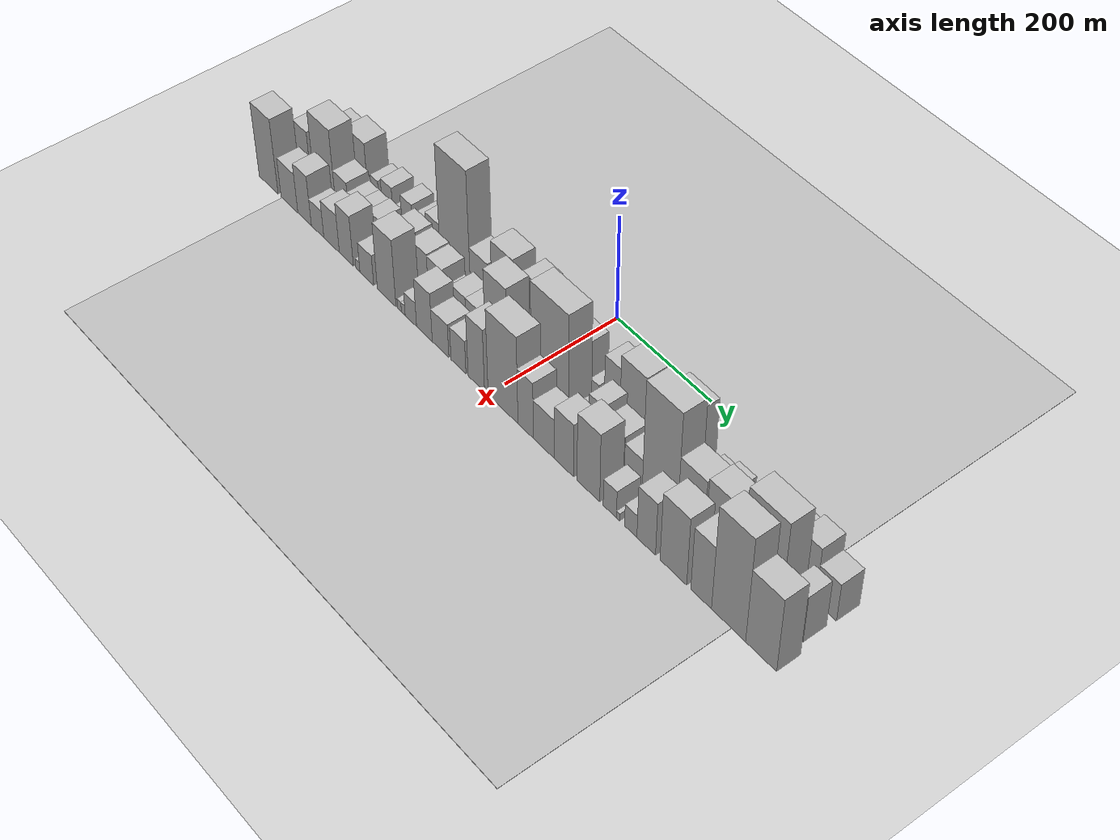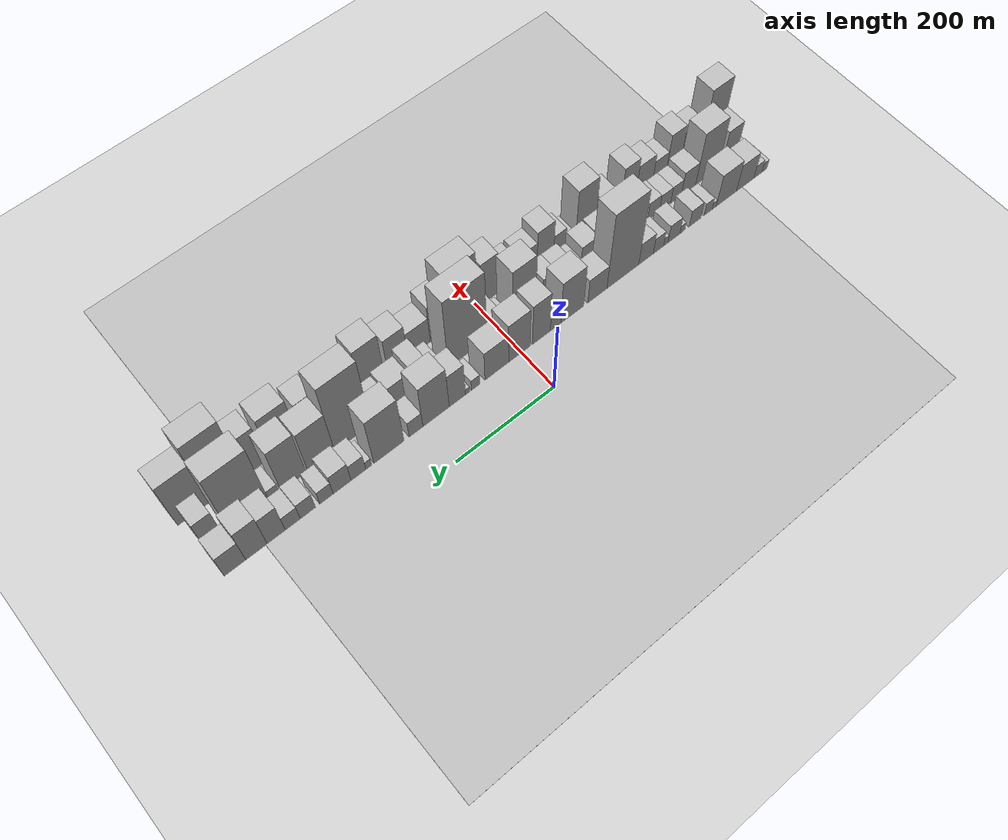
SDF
<?xml version="1.0" encoding="utf-8"?>

<sdf version="1.6">

   <world name="default">

      <gui fullscreen="0">

         <camera name="user_camera">

            <pose>-15 0 4.57585 0 0 0</pose>

            <view_controller>orbit</view_controller>

         </camera>

      </gui>

      <scene>

         <sky>

           <clouds>

             <speed>12</speed>

           </clouds>

         </sky>

         <ambient>0.4 0.4 0.4 1</ambient>

         <background>0.7 0.7 0.7 1</background>

         <shadows>1</shadows>

      </scene>

      <gravity>0 0 -9.8066</gravity>

      <magnetic_field>6e-06 2.3e-05 -4.2e-05</magnetic_field>

      <physics default="0" name="default_physics" type="ode">

         <ode>

            <solver>

               <type>quick</type>

               <iters>10</iters>

               <sor>1.0</sor>

               <use_dynamic_moi_rescaling>0</use_dynamic_moi_rescaling>

            </solver>

            <constraints>

               <cfm>0</cfm>

               <erp>0.2</erp>

               <contact_max_correcting_vel>100</contact_max_correcting_vel>

               <contact_surface_layer>0.001</contact_surface_layer>

            </constraints>

         </ode>

         <max_step_size>0.004</max_step_size>

         <real_time_factor>1</real_time_factor>

         <real_time_update_rate>250</real_time_update_rate>

      </physics>

      <light name="sun" type="directional">

         <cast_shadows>1</cast_shadows>

         <pose>0 0 10 0 0 0</pose>

         <diffuse>0.8 0.8 0.8 1</diffuse>

         <specular>0.2 0.2 0.2 1</specular>

         <attenuation>

            <range>1000</range>

            <constant>0.9</constant>

            <linear>0.01</linear>

            <quadratic>0.001</quadratic>

         </attenuation>

         <direction>-0.5 0.1 -0.9</direction>

      </light>

      <include>

         <name>ground_plane_1</name>

         <uri>model://HANNAS_ground_plane</uri>

         <pose>0 0 0  0 0 0</pose>

      </include>

      <include>

         <name>ground_plane_2</name>

         <uri>model://HANNAS_ground_plane</uri>

         <pose>100 0 0  0 0 0</pose>

      </include>

      <model name="building_1">

         <static>1</static>

         <pose frame="">100.0000 -553.8017 0 0.000000 0.000000 0.000000</pose>

         <link name="link">

            <pose frame="">0 0 13.50 0 0 0</pose>

            <collision name="collision">

               <geometry>

                  <box>

                     <size>40.0000 12.3965 27.0000</size>

                  </box>

               </geometry>

               <max_contacts>10</max_contacts>

               <surface>

                  <contact>

                     <ode/>

                  </contact>

                  <bounce/>

                  <friction>

                     <torsional>

                        <ode/>

                     </torsional>

                     <ode/>

                  </friction>

               </surface>

            </collision>

            <visual name="visual">

               <cast_shadows>0</cast_shadows>

               <geometry>

                  <box>

                     <size>40.0000 12.3965 27.0000</size>

                  </box>

               </geometry>

               <material>

                  <script>

                     <uri>model://HANNAS_wall/materials/scripts</uri>

                     <uri>model://HANNAS_wall/materials/textures</uri>

                     <name>vrc/HANNAS_wall</name>

                  </script>

               </material>

            </visual>

            <self_collide>0</self_collide>

            <enable_wind>0</enable_wind>

            <kinematic>0</kinematic>

         </link>

      </model>

      <model name="building_2">

         <static>1</static>

         <pose frame="">100.0000 -537.7084 0 0.000000 0.000000 0.000000</pose>

         <link name="link">

            <pose frame="">0 0 18.00 0 0 0</pose>

            <collision name="collision">

               <geometry>

                  <box>

                     <size>40.0000 19.7902 36.0000</size>

                  </box>

               </geometry>

               <max_contacts>10</max_contacts>

               <surface>

                  <contact>

                     <ode/>

                  </contact>

                  <bounce/>

                  <friction>

                     <torsional>

                        <ode/>

                     </torsional>

                     <ode/>

                  </friction>

               </surface>

            </collision>

            <visual name="visual">

               <cast_shadows>0</cast_shadows>

               <geometry>

                  <box>

                     <size>40.0000 19.7902 36.0000</size>

                  </box>

               </geometry>

               <material>

                  <script>

                     <uri>model://HANNAS_wall/materials/scripts</uri>

                     <uri>model://HANNAS_wall/materials/textures</uri>

                     <name>vrc/HANNAS_wall</name>

                  </script>

               </material>

            </visual>

            <self_collide>0</self_collide>

            <enable_wind>0</enable_wind>

            <kinematic>0</kinematic>

         </link>

      </model>

      <model name="building_3">

         <static>1</static>

         <pose frame="">100.0000 -506.4437 0 0.000000 0.000000 0.000000</pose>

         <link name="link">

            <pose frame="">0 0 37.50 0 0 0</pose>

            <collision name="collision">

               <geometry>

                  <box>

                     <size>40.0000 42.7392 75.0000</size>

                  </box>

               </geometry>

               <max_contacts>10</max_contacts>

               <surface>

                  <contact>

                     <ode/>

                  </contact>

                  <bounce/>

                  <friction>

                     <torsional>

                        <ode/>

                     </torsional>

                     <ode/>

                  </friction>

               </surface>

            </collision>

            <visual name="visual">

               <cast_shadows>0</cast_shadows>

               <geometry>

                  <box>

                     <size>40.0000 42.7392 75.0000</size>

                  </box>

               </geometry>

               <material>

                  <script>

                     <uri>model://HANNAS_wall/materials/scripts</uri>

                     <uri>model://HANNAS_wall/materials/textures</uri>

                     <name>vrc/HANNAS_wall</name>

                  </script>

               </material>

            </visual>

            <self_collide>0</self_collide>

            <enable_wind>0</enable_wind>

            <kinematic>0</kinematic>

         </link>

      </model>

      <model name="building_4">

         <static>1</static>

         <pose frame="">100.0000 -460.7238 0 0.000000 0.000000 0.000000</pose>

         <link name="link">

            <pose frame="">0 0 45.00 0 0 0</pose>

            <collision name="collision">

               <geometry>

                  <box>

                     <size>40.0000 48.7006 90.0000</size>

                  </box>

               </geometry>

               <max_contacts>10</max_contacts>

               <surface>

                  <contact>

                     <ode/>

                  </contact>

                  <bounce/>

                  <friction>

                     <torsional>

                        <ode/>

                     </torsional>

                     <ode/>

                  </friction>

               </surface>

            </collision>

            <visual name="visual">

               <cast_shadows>0</cast_shadows>

               <geometry>

                  <box>

                     <size>40.0000 48.7006 90.0000</size>

                  </box>

               </geometry>

               <material>

                  <script>

                     <uri>model://HANNAS_wall/materials/scripts</uri>

                     <uri>model://HANNAS_wall/materials/textures</uri>

                     <name>vrc/HANNAS_wall</name>

                  </script>

               </material>

            </visual>

            <self_collide>0</self_collide>

            <enable_wind>0</enable_wind>

            <kinematic>0</kinematic>

         </link>

      </model>

      <model name="building_5">

         <static>1</static>

         <pose frame="">100.0000 -431.5659 0 0.000000 0.000000 0.000000</pose>

         <link name="link">

            <pose frame="">0 0 10.50 0 0 0</pose>

            <collision name="collision">

               <geometry>

                  <box>

                     <size>40.0000 9.6152 21.0000</size>

                  </box>

               </geometry>

               <max_contacts>10</max_contacts>

               <surface>

                  <contact>

                     <ode/>

                  </contact>

                  <bounce/>

                  <friction>

                     <torsional>

                        <ode/>

                     </torsional>

                     <ode/>

                  </friction>

               </surface>

            </collision>

            <visual name="visual">

               <cast_shadows>0</cast_shadows>

               <geometry>

                  <box>

                     <size>40.0000 9.6152 21.0000</size>

                  </box>

               </geometry>

               <material>

                  <script>

                     <uri>model://HANNAS_wall/materials/scripts</uri>

                     <uri>model://HANNAS_wall/materials/textures</uri>

                     <name>vrc/HANNAS_wall</name>

                  </script>

               </material>

            </visual>

            <self_collide>0</self_collide>

            <enable_wind>0</enable_wind>

            <kinematic>0</kinematic>

         </link>

      </model>

      <model name="building_6">

         <static>1</static>

         <pose frame="">100.0000 -417.2465 0 0.000000 0.000000 0.000000</pose>

         <link name="link">

            <pose frame="">0 0 18.00 0 0 0</pose>

            <collision name="collision">

               <geometry>

                  <box>

                     <size>40.0000 19.0235 36.0000</size>

                  </box>

               </geometry>

               <max_contacts>10</max_contacts>

               <surface>

                  <contact>

                     <ode/>

                  </contact>

                  <bounce/>

                  <friction>

                     <torsional>

                        <ode/>

                     </torsional>

                     <ode/>

                  </friction>

               </surface>

            </collision>

            <visual name="visual">

               <cast_shadows>0</cast_shadows>

               <geometry>

                  <box>

                     <size>40.0000 19.0235 36.0000</size>

                  </box>

               </geometry>

               <material>

                  <script>

                     <uri>model://HANNAS_wall/materials/scripts</uri>

                     <uri>model://HANNAS_wall/materials/textures</uri>

                     <name>vrc/HANNAS_wall</name>

                  </script>

               </material>

            </visual>

            <self_collide>0</self_collide>

            <enable_wind>0</enable_wind>

            <kinematic>0</kinematic>

         </link>

      </model>

      <model name="building_7">

         <static>1</static>

         <pose frame="">100.0000 -386.0777 0 0.000000 0.000000 0.000000</pose>

         <link name="link">

            <pose frame="">0 0 24.00 0 0 0</pose>

            <collision name="collision">

               <geometry>

                  <box>

                     <size>40.0000 27.3142 48.0000</size>

                  </box>

               </geometry>

               <max_contacts>10</max_contacts>

               <surface>

                  <contact>

                     <ode/>

                  </contact>

                  <bounce/>

                  <friction>

                     <torsional>

                        <ode/>

                     </torsional>

                     <ode/>

                  </friction>

               </surface>

            </collision>

            <visual name="visual">

               <cast_shadows>0</cast_shadows>

               <geometry>

                  <box>

                     <size>40.0000 27.3142 48.0000</size>

                  </box>

               </geometry>

               <material>

                  <script>

                     <uri>model://HANNAS_wall/materials/scripts</uri>

                     <uri>model://HANNAS_wall/materials/textures</uri>

                     <name>vrc/HANNAS_wall</name>

                  </script>

               </material>

            </visual>

            <self_collide>0</self_collide>

            <enable_wind>0</enable_wind>

            <kinematic>0</kinematic>

         </link>

      </model>

      <model name="building_8">

         <static>1</static>

         <pose frame="">100.0000 -356.5520 0 0.000000 0.000000 0.000000</pose>

         <link name="link">

            <pose frame="">0 0 12.00 0 0 0</pose>

            <collision name="collision">

               <geometry>

                  <box>

                     <size>40.0000 11.7372 24.0000</size>

                  </box>

               </geometry>

               <max_contacts>10</max_contacts>

               <surface>

                  <contact>

                     <ode/>

                  </contact>

                  <bounce/>

                  <friction>

                     <torsional>

                        <ode/>

                     </torsional>

                     <ode/>

                  </friction>

               </surface>

            </collision>

            <visual name="visual">

               <cast_shadows>0</cast_shadows>

               <geometry>

                  <box>

                     <size>40.0000 11.7372 24.0000</size>

                  </box>

               </geometry>

               <material>

                  <script>

                     <uri>model://HANNAS_wall/materials/scripts</uri>

                     <uri>model://HANNAS_wall/materials/textures</uri>

                     <name>vrc/HANNAS_wall</name>

                  </script>

               </material>

            </visual>

            <self_collide>0</self_collide>

            <enable_wind>0</enable_wind>

            <kinematic>0</kinematic>

         </link>

      </model>

      <model name="building_9">

         <static>1</static>

         <pose frame="">100.0000 -336.7779 0 0.000000 0.000000 0.000000</pose>

         <link name="link">

            <pose frame="">0 0 25.50 0 0 0</pose>

            <collision name="collision">

               <geometry>

                  <box>

                     <size>40.0000 27.8112 51.0000</size>

                  </box>

               </geometry>

               <max_contacts>10</max_contacts>

               <surface>

                  <contact>

                     <ode/>

                  </contact>

                  <bounce/>

                  <friction>

                     <torsional>

                        <ode/>

                     </torsional>

                     <ode/>

                  </friction>

               </surface>

            </collision>

            <visual name="visual">

               <cast_shadows>0</cast_shadows>

               <geometry>

                  <box>

                     <size>40.0000 27.8112 51.0000</size>

                  </box>

               </geometry>

               <material>

                  <script>

                     <uri>model://HANNAS_wall/materials/scripts</uri>

                     <uri>model://HANNAS_wall/materials/textures</uri>

                     <name>vrc/HANNAS_wall</name>

                  </script>

               </material>

            </visual>

            <self_collide>0</self_collide>

            <enable_wind>0</enable_wind>

            <kinematic>0</kinematic>

         </link>

      </model>

      <model name="building_10">

         <static>1</static>

         <pose frame="">100.0000 -317.9994 0 0.000000 0.000000 0.000000</pose>

         <link name="link">

            <pose frame="">0 0 12.00 0 0 0</pose>

            <collision name="collision">

               <geometry>

                  <box>

                     <size>40.0000 9.7457 24.0000</size>

                  </box>

               </geometry>

               <max_contacts>10</max_contacts>

               <surface>

                  <contact>

                     <ode/>

                  </contact>

                  <bounce/>

                  <friction>

                     <torsional>

                        <ode/>

                     </torsional>

                     <ode/>

                  </friction>

               </surface>

            </collision>

            <visual name="visual">

               <cast_shadows>0</cast_shadows>

               <geometry>

                  <box>

                     <size>40.0000 9.7457 24.0000</size>

                  </box>

               </geometry>

               <material>

                  <script>

                     <uri>model://HANNAS_wall/materials/scripts</uri>

                     <uri>model://HANNAS_wall/materials/textures</uri>

                     <name>vrc/HANNAS_wall</name>

                  </script>

               </material>

            </visual>

            <self_collide>0</self_collide>

            <enable_wind>0</enable_wind>

            <kinematic>0</kinematic>

         </link>

      </model>

      <model name="building_11">

         <static>1</static>

         <pose frame="">100.0000 -301.2262 0 0.000000 0.000000 0.000000</pose>

         <link name="link">

            <pose frame="">0 0 22.50 0 0 0</pose>

            <collision name="collision">

               <geometry>

                  <box>

                     <size>40.0000 23.8006 45.0000</size>

                  </box>

               </geometry>

               <max_contacts>10</max_contacts>

               <surface>

                  <contact>

                     <ode/>

                  </contact>

                  <bounce/>

                  <friction>

                     <torsional>

                        <ode/>

                     </torsional>

                     <ode/>

                  </friction>

               </surface>

            </collision>

            <visual name="visual">

               <cast_shadows>0</cast_shadows>

               <geometry>

                  <box>

                     <size>40.0000 23.8006 45.0000</size>

                  </box>

               </geometry>

               <material>

                  <script>

                     <uri>model://HANNAS_wall/materials/scripts</uri>

                     <uri>model://HANNAS_wall/materials/textures</uri>

                     <name>vrc/HANNAS_wall</name>

                  </script>

               </material>

            </visual>

            <self_collide>0</self_collide>

            <enable_wind>0</enable_wind>

            <kinematic>0</kinematic>

         </link>

      </model>

      <model name="building_12">

         <static>1</static>

         <pose frame="">100.0000 -272.6169 0 0.000000 0.000000 0.000000</pose>

         <link name="link">

            <pose frame="">0 0 31.50 0 0 0</pose>

            <collision name="collision">

               <geometry>

                  <box>

                     <size>40.0000 33.4180 63.0000</size>

                  </box>

               </geometry>

               <max_contacts>10</max_contacts>

               <surface>

                  <contact>

                     <ode/>

                  </contact>

                  <bounce/>

                  <friction>

                     <torsional>

                        <ode/>

                     </torsional>

                     <ode/>

                  </friction>

               </surface>

            </collision>

            <visual name="visual">

               <cast_shadows>0</cast_shadows>

               <geometry>

                  <box>

                     <size>40.0000 33.4180 63.0000</size>

                  </box>

               </geometry>

               <material>

                  <script>

                     <uri>model://HANNAS_wall/materials/scripts</uri>

                     <uri>model://HANNAS_wall/materials/textures</uri>

                     <name>vrc/HANNAS_wall</name>

                  </script>

               </material>

            </visual>

            <self_collide>0</self_collide>

            <enable_wind>0</enable_wind>

            <kinematic>0</kinematic>

         </link>

      </model>

      <model name="building_13">

         <static>1</static>

         <pose frame="">100.0000 -220.0636 0 0.000000 0.000000 0.000000</pose>

         <link name="link">

            <pose frame="">0 0 109.50 0 0 0</pose>

            <collision name="collision">

               <geometry>

                  <box>

                     <size>40.0000 71.6887 219.0000</size>

                  </box>

               </geometry>

               <max_contacts>10</max_contacts>

               <surface>

                  <contact>

                     <ode/>

                  </contact>

                  <bounce/>

                  <friction>

                     <torsional>

                        <ode/>

                     </torsional>

                     <ode/>

                  </friction>

               </surface>

            </collision>

            <visual name="visual">

               <cast_shadows>0</cast_shadows>

               <geometry>

                  <box>

                     <size>40.0000 71.6887 219.0000</size>

                  </box>

               </geometry>

               <material>

                  <script>

                     <uri>model://HANNAS_wall/materials/scripts</uri>

                     <uri>model://HANNAS_wall/materials/textures</uri>

                     <name>vrc/HANNAS_wall</name>

                  </script>

               </material>

            </visual>

            <self_collide>0</self_collide>

            <enable_wind>0</enable_wind>

            <kinematic>0</kinematic>

         </link>

      </model>

      <model name="building_14">

         <static>1</static>

         <pose frame="">100.0000 -163.1193 0 0.000000 0.000000 0.000000</pose>

         <link name="link">

            <pose frame="">0 0 36.00 0 0 0</pose>

            <collision name="collision">

               <geometry>

                  <box>

                     <size>40.0000 42.1997 72.0000</size>

                  </box>

               </geometry>

               <max_contacts>10</max_contacts>

               <surface>

                  <contact>

                     <ode/>

                  </contact>

                  <bounce/>

                  <friction>

                     <torsional>

                        <ode/>

                     </torsional>

                     <ode/>

                  </friction>

               </surface>

            </collision>

            <visual name="visual">

               <cast_shadows>0</cast_shadows>

               <geometry>

                  <box>

                     <size>40.0000 42.1997 72.0000</size>

                  </box>

               </geometry>

               <material>

                  <script>

                     <uri>model://HANNAS_wall/materials/scripts</uri>

                     <uri>model://HANNAS_wall/materials/textures</uri>

                     <name>vrc/HANNAS_wall</name>

                  </script>

               </material>

            </visual>

            <self_collide>0</self_collide>

            <enable_wind>0</enable_wind>

            <kinematic>0</kinematic>

         </link>

      </model>

      <model name="building_15">

         <static>1</static>

         <pose frame="">100.0000 -108.1530 0 0.000000 0.000000 0.000000</pose>

         <link name="link">

            <pose frame="">0 0 63.00 0 0 0</pose>

            <collision name="collision">

               <geometry>

                  <box>

                     <size>40.0000 49.7329 126.0000</size>

                  </box>

               </geometry>

               <max_contacts>10</max_contacts>

               <surface>

                  <contact>

                     <ode/>

                  </contact>

                  <bounce/>

                  <friction>

                     <torsional>

                        <ode/>

                     </torsional>

                     <ode/>

                  </friction>

               </surface>

            </collision>

            <visual name="visual">

               <cast_shadows>0</cast_shadows>

               <geometry>

                  <box>

                     <size>40.0000 49.7329 126.0000</size>

                  </box>

               </geometry>

               <material>

                  <script>

                     <uri>model://HANNAS_wall/materials/scripts</uri>

                     <uri>model://HANNAS_wall/materials/textures</uri>

                     <name>vrc/HANNAS_wall</name>

                  </script>

               </material>

            </visual>

            <self_collide>0</self_collide>

            <enable_wind>0</enable_wind>

            <kinematic>0</kinematic>

         </link>

      </model>

      <model name="building_16">

         <static>1</static>

         <pose frame="">100.0000 -72.0409 0 0.000000 0.000000 0.000000</pose>

         <link name="link">

            <pose frame="">0 0 19.50 0 0 0</pose>

            <collision name="collision">

               <geometry>

                  <box>

                     <size>40.0000 22.4915 39.0000</size>

                  </box>

               </geometry>

               <max_contacts>10</max_contacts>

               <surface>

                  <contact>

                     <ode/>

                  </contact>

                  <bounce/>

                  <friction>

                     <torsional>

                        <ode/>

                     </torsional>

                     <ode/>

                  </friction>

               </surface>

            </collision>

            <visual name="visual">

               <cast_shadows>0</cast_shadows>

               <geometry>

                  <box>

                     <size>40.0000 22.4915 39.0000</size>

                  </box>

               </geometry>

               <material>

                  <script>

                     <uri>model://HANNAS_wall/materials/scripts</uri>

                     <uri>model://HANNAS_wall/materials/textures</uri>

                     <name>vrc/HANNAS_wall</name>

                  </script>

               </material>

            </visual>

            <self_collide>0</self_collide>

            <enable_wind>0</enable_wind>

            <kinematic>0</kinematic>

         </link>

      </model>

      <model name="building_17">

         <static>1</static>

         <pose frame="">100.0000 -41.7449 0 0.000000 0.000000 0.000000</pose>

         <link name="link">

            <pose frame="">0 0 61.50 0 0 0</pose>

            <collision name="collision">

               <geometry>

                  <box>

                     <size>40.0000 38.1003 123.0000</size>

                  </box>

               </geometry>

               <max_contacts>10</max_contacts>

               <surface>

                  <contact>

                     <ode/>

                  </contact>

                  <bounce/>

                  <friction>

                     <torsional>

                        <ode/>

                     </torsional>

                     <ode/>

                  </friction>

               </surface>

            </collision>

            <visual name="visual">

               <cast_shadows>0</cast_shadows>

               <geometry>

                  <box>

                     <size>40.0000 38.1003 123.0000</size>

                  </box>

               </geometry>

               <material>

                  <script>

                     <uri>model://HANNAS_wall/materials/scripts</uri>

                     <uri>model://HANNAS_wall/materials/textures</uri>

                     <name>vrc/HANNAS_wall</name>

                  </script>

               </material>

            </visual>

            <self_collide>0</self_collide>

            <enable_wind>0</enable_wind>

            <kinematic>0</kinematic>

         </link>

      </model>

      <model name="building_18">

         <static>1</static>

         <pose frame="">100.0000 4.8909 0 0.000000 0.000000 0.000000</pose>

         <link name="link">

            <pose frame="">0 0 60.00 0 0 0</pose>

            <collision name="collision">

               <geometry>

                  <box>

                     <size>40.0000 45.1713 120.0000</size>

                  </box>

               </geometry>

               <max_contacts>10</max_contacts>

               <surface>

                  <contact>

                     <ode/>

                  </contact>

                  <bounce/>

                  <friction>

                     <torsional>

                        <ode/>

                     </torsional>

                     <ode/>

                  </friction>

               </surface>

            </collision>

            <visual name="visual">

               <cast_shadows>0</cast_shadows>

               <geometry>

                  <box>

                     <size>40.0000 45.1713 120.0000</size>

                  </box>

               </geometry>

               <material>

                  <script>

                     <uri>model://HANNAS_wall/materials/scripts</uri>

                     <uri>model://HANNAS_wall/materials/textures</uri>

                     <name>vrc/HANNAS_wall</name>

                  </script>

               </material>

            </visual>

            <self_collide>0</self_collide>

            <enable_wind>0</enable_wind>

            <kinematic>0</kinematic>

         </link>

      </model>

      <model name="building_19">

         <static>1</static>

         <pose frame="">100.0000 52.0612 0 0.000000 0.000000 0.000000</pose>

         <link name="link">

            <pose frame="">0 0 45.00 0 0 0</pose>

            <collision name="collision">

               <geometry>

                  <box>

                     <size>40.0000 49.1694 90.0000</size>

                  </box>

               </geometry>

               <max_contacts>10</max_contacts>

               <surface>

                  <contact>

                     <ode/>

                  </contact>

                  <bounce/>

                  <friction>

                     <torsional>

                        <ode/>

                     </torsional>

                     <ode/>

                  </friction>

               </surface>

            </collision>

            <visual name="visual">

               <cast_shadows>0</cast_shadows>

               <geometry>

                  <box>

                     <size>40.0000 49.1694 90.0000</size>

                  </box>

               </geometry>

               <material>

                  <script>

                     <uri>model://HANNAS_wall/materials/scripts</uri>

                     <uri>model://HANNAS_wall/materials/textures</uri>

                     <name>vrc/HANNAS_wall</name>

                  </script>

               </material>

            </visual>

            <self_collide>0</self_collide>

            <enable_wind>0</enable_wind>

            <kinematic>0</kinematic>

         </link>

      </model>

      <model name="building_20">

         <static>1</static>

         <pose frame="">100.0000 95.6489 0 0.000000 0.000000 0.000000</pose>

         <link name="link">

            <pose frame="">0 0 16.50 0 0 0</pose>

            <collision name="collision">

               <geometry>

                  <box>

                     <size>40.0000 18.0059 33.0000</size>

                  </box>

               </geometry>

               <max_contacts>10</max_contacts>

               <surface>

                  <contact>

                     <ode/>

                  </contact>

                  <bounce/>

                  <friction>

                     <torsional>

                        <ode/>

                     </torsional>

                     <ode/>

                  </friction>

               </surface>

            </collision>

            <visual name="visual">

               <cast_shadows>0</cast_shadows>

               <geometry>

                  <box>

                     <size>40.0000 18.0059 33.0000</size>

                  </box>

               </geometry>

               <material>

                  <script>

                     <uri>model://HANNAS_wall/materials/scripts</uri>

                     <uri>model://HANNAS_wall/materials/textures</uri>

                     <name>vrc/HANNAS_wall</name>

                  </script>

               </material>

            </visual>

            <self_collide>0</self_collide>

            <enable_wind>0</enable_wind>

            <kinematic>0</kinematic>

         </link>

      </model>

      <model name="building_21">

         <static>1</static>

         <pose frame="">100.0000 111.9884 0 0.000000 0.000000 0.000000</pose>

         <link name="link">

            <pose frame="">0 0 9.00 0 0 0</pose>

            <collision name="collision">

               <geometry>

                  <box>

                     <size>40.0000 8.6732 18.0000</size>

                  </box>

               </geometry>

               <max_contacts>10</max_contacts>

               <surface>

                  <contact>

                     <ode/>

                  </contact>

                  <bounce/>

                  <friction>

                     <torsional>

                        <ode/>

                     </torsional>

                     <ode/>

                  </friction>

               </surface>

            </collision>

            <visual name="visual">

               <cast_shadows>0</cast_shadows>

               <geometry>

                  <box>

                     <size>40.0000 8.6732 18.0000</size>

                  </box>

               </geometry>

               <material>

                  <script>

                     <uri>model://HANNAS_wall/materials/scripts</uri>

                     <uri>model://HANNAS_wall/materials/textures</uri>

                     <name>vrc/HANNAS_wall</name>

                  </script>

               </material>

            </visual>

            <self_collide>0</self_collide>

            <enable_wind>0</enable_wind>

            <kinematic>0</kinematic>

         </link>

      </model>

      <model name="building_22">

         <static>1</static>

         <pose frame="">100.0000 132.8876 0 0.000000 0.000000 0.000000</pose>

         <link name="link">

            <pose frame="">0 0 52.50 0 0 0</pose>

            <collision name="collision">

               <geometry>

                  <box>

                     <size>40.0000 33.1251 105.0000</size>

                  </box>

               </geometry>

               <max_contacts>10</max_contacts>

               <surface>

                  <contact>

                     <ode/>

                  </contact>

                  <bounce/>

                  <friction>

                     <torsional>

                        <ode/>

                     </torsional>

                     <ode/>

                  </friction>

               </surface>

            </collision>

            <visual name="visual">

               <cast_shadows>0</cast_shadows>

               <geometry>

                  <box>

                     <size>40.0000 33.1251 105.0000</size>

                  </box>

               </geometry>

               <material>

                  <script>

                     <uri>model://HANNAS_wall/materials/scripts</uri>

                     <uri>model://HANNAS_wall/materials/textures</uri>

                     <name>vrc/HANNAS_wall</name>

                  </script>

               </material>

            </visual>

            <self_collide>0</self_collide>

            <enable_wind>0</enable_wind>

            <kinematic>0</kinematic>

         </link>

      </model>

      <model name="building_23">

         <static>1</static>

         <pose frame="">100.0000 175.6709 0 0.000000 0.000000 0.000000</pose>

         <link name="link">

            <pose frame="">0 0 66.00 0 0 0</pose>

            <collision name="collision">

               <geometry>

                  <box>

                     <size>40.0000 52.4415 132.0000</size>

                  </box>

               </geometry>

               <max_contacts>10</max_contacts>

               <surface>

                  <contact>

                     <ode/>

                  </contact>

                  <bounce/>

                  <friction>

                     <torsional>

                        <ode/>

                     </torsional>

                     <ode/>

                  </friction>

               </surface>

            </collision>

            <visual name="visual">

               <cast_shadows>0</cast_shadows>

               <geometry>

                  <box>

                     <size>40.0000 52.4415 132.0000</size>

                  </box>

               </geometry>

               <material>

                  <script>

                     <uri>model://HANNAS_wall/materials/scripts</uri>

                     <uri>model://HANNAS_wall/materials/textures</uri>

                     <name>vrc/HANNAS_wall</name>

                  </script>

               </material>

            </visual>

            <self_collide>0</self_collide>

            <enable_wind>0</enable_wind>

            <kinematic>0</kinematic>

         </link>

      </model>

      <model name="building_24">

         <static>1</static>

         <pose frame="">100.0000 215.5347 0 0.000000 0.000000 0.000000</pose>

         <link name="link">

            <pose frame="">0 0 25.50 0 0 0</pose>

            <collision name="collision">

               <geometry>

                  <box>

                     <size>40.0000 27.2861 51.0000</size>

                  </box>

               </geometry>

               <max_contacts>10</max_contacts>

               <surface>

                  <contact>

                     <ode/>

                  </contact>

                  <bounce/>

                  <friction>

                     <torsional>

                        <ode/>

                     </torsional>

                     <ode/>

                  </friction>

               </surface>

            </collision>

            <visual name="visual">

               <cast_shadows>0</cast_shadows>

               <geometry>

                  <box>

                     <size>40.0000 27.2861 51.0000</size>

                  </box>

               </geometry>

               <material>

                  <script>

                     <uri>model://HANNAS_wall/materials/scripts</uri>

                     <uri>model://HANNAS_wall/materials/textures</uri>

                     <name>vrc/HANNAS_wall</name>

                  </script>

               </material>

            </visual>

            <self_collide>0</self_collide>

            <enable_wind>0</enable_wind>

            <kinematic>0</kinematic>

         </link>

      </model>

      <model name="building_25">

         <static>1</static>

         <pose frame="">100.0000 268.4936 0 0.000000 0.000000 0.000000</pose>

         <link name="link">

            <pose frame="">0 0 75.00 0 0 0</pose>

            <collision name="collision">

               <geometry>

                  <box>

                     <size>40.0000 58.6317 150.0000</size>

                  </box>

               </geometry>

               <max_contacts>10</max_contacts>

               <surface>

                  <contact>

                     <ode/>

                  </contact>

                  <bounce/>

                  <friction>

                     <torsional>

                        <ode/>

                     </torsional>

                     <ode/>

                  </friction>

               </surface>

            </collision>

            <visual name="visual">

               <cast_shadows>0</cast_shadows>

               <geometry>

                  <box>

                     <size>40.0000 58.6317 150.0000</size>

                  </box>

               </geometry>

               <material>

                  <script>

                     <uri>model://HANNAS_wall/materials/scripts</uri>

                     <uri>model://HANNAS_wall/materials/textures</uri>

                     <name>vrc/HANNAS_wall</name>

                  </script>

               </material>

            </visual>

            <self_collide>0</self_collide>

            <enable_wind>0</enable_wind>

            <kinematic>0</kinematic>

         </link>

      </model>

      <model name="building_26">

         <static>1</static>

         <pose frame="">100.0000 307.4521 0 0.000000 0.000000 0.000000</pose>

         <link name="link">

            <pose frame="">0 0 13.50 0 0 0</pose>

            <collision name="collision">

               <geometry>

                  <box>

                     <size>40.0000 11.2853 27.0000</size>

                  </box>

               </geometry>

               <max_contacts>10</max_contacts>

               <surface>

                  <contact>

                     <ode/>

                  </contact>

                  <bounce/>

                  <friction>

                     <torsional>

                        <ode/>

                     </torsional>

                     <ode/>

                  </friction>

               </surface>

            </collision>

            <visual name="visual">

               <cast_shadows>0</cast_shadows>

               <geometry>

                  <box>

                     <size>40.0000 11.2853 27.0000</size>

                  </box>

               </geometry>

               <material>

                  <script>

                     <uri>model://HANNAS_wall/materials/scripts</uri>

                     <uri>model://HANNAS_wall/materials/textures</uri>

                     <name>vrc/HANNAS_wall</name>

                  </script>

               </material>

            </visual>

            <self_collide>0</self_collide>

            <enable_wind>0</enable_wind>

            <kinematic>0</kinematic>

         </link>

      </model>

      <model name="building_27">

         <static>1</static>

         <pose frame="">100.0000 327.2081 0 0.000000 0.000000 0.000000</pose>

         <link name="link">

            <pose frame="">0 0 27.00 0 0 0</pose>

            <collision name="collision">

               <geometry>

                  <box>

                     <size>40.0000 28.2266 54.0000</size>

                  </box>

               </geometry>

               <max_contacts>10</max_contacts>

               <surface>

                  <contact>

                     <ode/>

                  </contact>

                  <bounce/>

                  <friction>

                     <torsional>

                        <ode/>

                     </torsional>

                     <ode/>

                  </friction>

               </surface>

            </collision>

            <visual name="visual">

               <cast_shadows>0</cast_shadows>

               <geometry>

                  <box>

                     <size>40.0000 28.2266 54.0000</size>

                  </box>

               </geometry>

               <material>

                  <script>

                     <uri>model://HANNAS_wall/materials/scripts</uri>

                     <uri>model://HANNAS_wall/materials/textures</uri>

                     <name>vrc/HANNAS_wall</name>

                  </script>

               </material>

            </visual>

            <self_collide>0</self_collide>

            <enable_wind>0</enable_wind>

            <kinematic>0</kinematic>

         </link>

      </model>

      <model name="building_28">

         <static>1</static>

         <pose frame="">100.0000 358.2959 0 0.000000 0.000000 0.000000</pose>

         <link name="link">

            <pose frame="">0 0 33.00 0 0 0</pose>

            <collision name="collision">

               <geometry>

                  <box>

                     <size>40.0000 33.9491 66.0000</size>

                  </box>

               </geometry>

               <max_contacts>10</max_contacts>

               <surface>

                  <contact>

                     <ode/>

                  </contact>

                  <bounce/>

                  <friction>

                     <torsional>

                        <ode/>

                     </torsional>

                     <ode/>

                  </friction>

               </surface>

            </collision>

            <visual name="visual">

               <cast_shadows>0</cast_shadows>

               <geometry>

                  <box>

                     <size>40.0000 33.9491 66.0000</size>

                  </box>

               </geometry>

               <material>

                  <script>

                     <uri>model://HANNAS_wall/materials/scripts</uri>

                     <uri>model://HANNAS_wall/materials/textures</uri>

                     <name>vrc/HANNAS_wall</name>

                  </script>

               </material>

            </visual>

            <self_collide>0</self_collide>

            <enable_wind>0</enable_wind>

            <kinematic>0</kinematic>

         </link>

      </model>

      <model name="building_29">

         <static>1</static>

         <pose frame="">100.0000 387.8165 0 0.000000 0.000000 0.000000</pose>

         <link name="link">

            <pose frame="">0 0 22.50 0 0 0</pose>

            <collision name="collision">

               <geometry>

                  <box>

                     <size>40.0000 25.0919 45.0000</size>

                  </box>

               </geometry>

               <max_contacts>10</max_contacts>

               <surface>

                  <contact>

                     <ode/>

                  </contact>

                  <bounce/>

                  <friction>

                     <torsional>

                        <ode/>

                     </torsional>

                     <ode/>

                  </friction>

               </surface>

            </collision>

            <visual name="visual">

               <cast_shadows>0</cast_shadows>

               <geometry>

                  <box>

                     <size>40.0000 25.0919 45.0000</size>

                  </box>

               </geometry>

               <material>

                  <script>

                     <uri>model://HANNAS_wall/materials/scripts</uri>

                     <uri>model://HANNAS_wall/materials/textures</uri>

                     <name>vrc/HANNAS_wall</name>

                  </script>

               </material>

            </visual>

            <self_collide>0</self_collide>

            <enable_wind>0</enable_wind>

            <kinematic>0</kinematic>

         </link>

      </model>

      <model name="building_30">

         <static>1</static>

         <pose frame="">100.0000 422.3995 0 0.000000 0.000000 0.000000</pose>

         <link name="link">

            <pose frame="">0 0 27.00 0 0 0</pose>

            <collision name="collision">

               <geometry>

                  <box>

                     <size>40.0000 28.0742 54.0000</size>

                  </box>

               </geometry>

               <max_contacts>10</max_contacts>

               <surface>

                  <contact>

                     <ode/>

                  </contact>

                  <bounce/>

                  <friction>

                     <torsional>

                        <ode/>

                     </torsional>

                     <ode/>

                  </friction>

               </surface>

            </collision>

            <visual name="visual">

               <cast_shadows>0</cast_shadows>

               <geometry>

                  <box>

                     <size>40.0000 28.0742 54.0000</size>

                  </box>

               </geometry>

               <material>

                  <script>

                     <uri>model://HANNAS_wall/materials/scripts</uri>

                     <uri>model://HANNAS_wall/materials/textures</uri>

                     <name>vrc/HANNAS_wall</name>

                  </script>

               </material>

            </visual>

            <self_collide>0</self_collide>

            <enable_wind>0</enable_wind>

            <kinematic>0</kinematic>

         </link>

      </model>

      <model name="building_31">

         <static>1</static>

         <pose frame="">100.0000 450.1363 0 0.000000 0.000000 0.000000</pose>

         <link name="link">

            <pose frame="">0 0 24.00 0 0 0</pose>

            <collision name="collision">

               <geometry>

                  <box>

                     <size>40.0000 27.3993 48.0000</size>

                  </box>

               </geometry>

               <max_contacts>10</max_contacts>

               <surface>

                  <contact>

                     <ode/>

                  </contact>

                  <bounce/>

                  <friction>

                     <torsional>

                        <ode/>

                     </torsional>

                     <ode/>

                  </friction>

               </surface>

            </collision>

            <visual name="visual">

               <cast_shadows>0</cast_shadows>

               <geometry>

                  <box>

                     <size>40.0000 27.3993 48.0000</size>

                  </box>

               </geometry>

               <material>

                  <script>

                     <uri>model://HANNAS_wall/materials/scripts</uri>

                     <uri>model://HANNAS_wall/materials/textures</uri>

                     <name>vrc/HANNAS_wall</name>

                  </script>

               </material>

            </visual>

            <self_collide>0</self_collide>

            <enable_wind>0</enable_wind>

            <kinematic>0</kinematic>

         </link>

      </model>

      <model name="building_32">

         <static>1</static>

         <pose frame="">100.0000 480.4484 0 0.000000 0.000000 0.000000</pose>

         <link name="link">

            <pose frame="">0 0 48.00 0 0 0</pose>

            <collision name="collision">

               <geometry>

                  <box>

                     <size>40.0000 33.2249 96.0000</size>

                  </box>

               </geometry>

               <max_contacts>10</max_contacts>

               <surface>

                  <contact>

                     <ode/>

                  </contact>

                  <bounce/>

                  <friction>

                     <torsional>

                        <ode/>

                     </torsional>

                     <ode/>

                  </friction>

               </surface>

            </collision>

            <visual name="visual">

               <cast_shadows>0</cast_shadows>

               <geometry>

                  <box>

                     <size>40.0000 33.2249 96.0000</size>

                  </box>

               </geometry>

               <material>

                  <script>

                     <uri>model://HANNAS_wall/materials/scripts</uri>

                     <uri>model://HANNAS_wall/materials/textures</uri>

                     <name>vrc/HANNAS_wall</name>

                  </script>

               </material>

            </visual>

            <self_collide>0</self_collide>

            <enable_wind>0</enable_wind>

            <kinematic>0</kinematic>

         </link>

      </model>

      <model name="building_33">

         <static>1</static>

         <pose frame="">100.0000 516.2887 0 0.000000 0.000000 0.000000</pose>

         <link name="link">

            <pose frame="">0 0 54.00 0 0 0</pose>

            <collision name="collision">

               <geometry>

                  <box>

                     <size>40.0000 38.4556 108.0000</size>

                  </box>

               </geometry>

               <max_contacts>10</max_contacts>

               <surface>

                  <contact>

                     <ode/>

                  </contact>

                  <bounce/>

                  <friction>

                     <torsional>

                        <ode/>

                     </torsional>

                     <ode/>

                  </friction>

               </surface>

            </collision>

            <visual name="visual">

               <cast_shadows>0</cast_shadows>

               <geometry>

                  <box>

                     <size>40.0000 38.4556 108.0000</size>

                  </box>

               </geometry>

               <material>

                  <script>

                     <uri>model://HANNAS_wall/materials/scripts</uri>

                     <uri>model://HANNAS_wall/materials/textures</uri>

                     <name>vrc/HANNAS_wall</name>

                  </script>

               </material>

            </visual>

            <self_collide>0</self_collide>

            <enable_wind>0</enable_wind>

            <kinematic>0</kinematic>

         </link>

      </model>

      <model name="building_34">

         <static>1</static>

         <pose frame="">100.0000 554.6955 0 0.000000 0.000000 0.000000</pose>

         <link name="link">

            <pose frame="">0 0 37.50 0 0 0</pose>

            <collision name="collision">

               <geometry>

                  <box>

                     <size>40.0000 38.3582 75.0000</size>

                  </box>

               </geometry>

               <max_contacts>10</max_contacts>

               <surface>

                  <contact>

                     <ode/>

                  </contact>

                  <bounce/>

                  <friction>

                     <torsional>

                        <ode/>

                     </torsional>

                     <ode/>

                  </friction>

               </surface>

            </collision>

            <visual name="visual">

               <cast_shadows>0</cast_shadows>

               <geometry>

                  <box>

                     <size>40.0000 38.3582 75.0000</size>

                  </box>

               </geometry>

               <material>

                  <script>

                     <uri>model://HANNAS_wall/materials/scripts</uri>

                     <uri>model://HANNAS_wall/materials/textures</uri>

                     <name>vrc/HANNAS_wall</name>

                  </script>

               </material>

            </visual>

            <self_collide>0</self_collide>

            <enable_wind>0</enable_wind>

            <kinematic>0</kinematic>

         </link>

      </model>

      <model name="building_35">

         <static>1</static>

         <pose frame="">155.0000 -547.6633 0 0.000000 0.000000 0.000000</pose>

         <link name="link">

            <pose frame="">0 0 15.00 0 0 0</pose>

            <collision name="collision">

               <geometry>

                  <box>

                     <size>40.0000 16.6734 30.0000</size>

                  </box>

               </geometry>

               <max_contacts>10</max_contacts>

               <surface>

                  <contact>

                     <ode/>

                  </contact>

                  <bounce/>

                  <friction>

                     <torsional>

                        <ode/>

                     </torsional>

                     <ode/>

                  </friction>

               </surface>

            </collision>

            <visual name="visual">

               <cast_shadows>0</cast_shadows>

               <geometry>

                  <box>

                     <size>40.0000 16.6734 30.0000</size>

                  </box>

               </geometry>

               <material>

                  <script>

                     <uri>model://HANNAS_wall/materials/scripts</uri>

                     <uri>model://HANNAS_wall/materials/textures</uri>

                     <name>vrc/HANNAS_wall</name>

                  </script>

               </material>

            </visual>

            <self_collide>0</self_collide>

            <enable_wind>0</enable_wind>

            <kinematic>0</kinematic>

         </link>

      </model>

      <model name="building_36">

         <static>1</static>

         <pose frame="">155.0000 -521.5033 0 0.000000 0.000000 0.000000</pose>

         <link name="link">

            <pose frame="">0 0 48.00 0 0 0</pose>

            <collision name="collision">

               <geometry>

                  <box>

                     <size>40.0000 35.6466 96.0000</size>

                  </box>

               </geometry>

               <max_contacts>10</max_contacts>

               <surface>

                  <contact>

                     <ode/>

                  </contact>

                  <bounce/>

                  <friction>

                     <torsional>

                        <ode/>

                     </torsional>

                     <ode/>

                  </friction>

               </surface>

            </collision>

            <visual name="visual">

               <cast_shadows>0</cast_shadows>

               <geometry>

                  <box>

                     <size>40.0000 35.6466 96.0000</size>

                  </box>

               </geometry>

               <material>

                  <script>

                     <uri>model://HANNAS_wall/materials/scripts</uri>

                     <uri>model://HANNAS_wall/materials/textures</uri>

                     <name>vrc/HANNAS_wall</name>

                  </script>

               </material>

            </visual>

            <self_collide>0</self_collide>

            <enable_wind>0</enable_wind>

            <kinematic>0</kinematic>

         </link>

      </model>

      <model name="building_37">

         <static>1</static>

         <pose frame="">155.0000 -499.4806 0 0.000000 0.000000 0.000000</pose>

         <link name="link">

            <pose frame="">0 0 9.00 0 0 0</pose>

            <collision name="collision">

               <geometry>

                  <box>

                     <size>40.0000 8.3988 18.0000</size>

                  </box>

               </geometry>

               <max_contacts>10</max_contacts>

               <surface>

                  <contact>

                     <ode/>

                  </contact>

                  <bounce/>

                  <friction>

                     <torsional>

                        <ode/>

                     </torsional>

                     <ode/>

                  </friction>

               </surface>

            </collision>

            <visual name="visual">

               <cast_shadows>0</cast_shadows>

               <geometry>

                  <box>

                     <size>40.0000 8.3988 18.0000</size>

                  </box>

               </geometry>

               <material>

                  <script>

                     <uri>model://HANNAS_wall/materials/scripts</uri>

                     <uri>model://HANNAS_wall/materials/textures</uri>

                     <name>vrc/HANNAS_wall</name>

                  </script>

               </material>

            </visual>

            <self_collide>0</self_collide>

            <enable_wind>0</enable_wind>

            <kinematic>0</kinematic>

         </link>

      </model>

      <model name="building_38">

         <static>1</static>

         <pose frame="">155.0000 -467.8850 0 0.000000 0.000000 0.000000</pose>

         <link name="link">

            <pose frame="">0 0 72.00 0 0 0</pose>

            <collision name="collision">

               <geometry>

                  <box>

                     <size>40.0000 54.7925 144.0000</size>

                  </box>

               </geometry>

               <max_contacts>10</max_contacts>

               <surface>

                  <contact>

                     <ode/>

                  </contact>

                  <bounce/>

                  <friction>

                     <torsional>

                        <ode/>

                     </torsional>

                     <ode/>

                  </friction>

               </surface>

            </collision>

            <visual name="visual">

               <cast_shadows>0</cast_shadows>

               <geometry>

                  <box>

                     <size>40.0000 54.7925 144.0000</size>

                  </box>

               </geometry>

               <material>

                  <script>

                     <uri>model://HANNAS_wall/materials/scripts</uri>

                     <uri>model://HANNAS_wall/materials/textures</uri>

                     <name>vrc/HANNAS_wall</name>

                  </script>

               </material>

            </visual>

            <self_collide>0</self_collide>

            <enable_wind>0</enable_wind>

            <kinematic>0</kinematic>

         </link>

      </model>

      <model name="building_39">

         <static>1</static>

         <pose frame="">155.0000 -423.4270 0 0.000000 0.000000 0.000000</pose>

         <link name="link">

            <pose frame="">0 0 33.00 0 0 0</pose>

            <collision name="collision">

               <geometry>

                  <box>

                     <size>40.0000 34.1236 66.0000</size>

                  </box>

               </geometry>

               <max_contacts>10</max_contacts>

               <surface>

                  <contact>

                     <ode/>

                  </contact>

                  <bounce/>

                  <friction>

                     <torsional>

                        <ode/>

                     </torsional>

                     <ode/>

                  </friction>

               </surface>

            </collision>

            <visual name="visual">

               <cast_shadows>0</cast_shadows>

               <geometry>

                  <box>

                     <size>40.0000 34.1236 66.0000</size>

                  </box>

               </geometry>

               <material>

                  <script>

                     <uri>model://HANNAS_wall/materials/scripts</uri>

                     <uri>model://HANNAS_wall/materials/textures</uri>

                     <name>vrc/HANNAS_wall</name>

                  </script>

               </material>

            </visual>

            <self_collide>0</self_collide>

            <enable_wind>0</enable_wind>

            <kinematic>0</kinematic>

         </link>

      </model>

      <model name="building_40">

         <static>1</static>

         <pose frame="">155.0000 -393.9571 0 0.000000 0.000000 0.000000</pose>

         <link name="link">

            <pose frame="">0 0 24.00 0 0 0</pose>

            <collision name="collision">

               <geometry>

                  <box>

                     <size>40.0000 24.8163 48.0000</size>

                  </box>

               </geometry>

               <max_contacts>10</max_contacts>

               <surface>

                  <contact>

                     <ode/>

                  </contact>

                  <bounce/>

                  <friction>

                     <torsional>

                        <ode/>

                     </torsional>

                     <ode/>

                  </friction>

               </surface>

            </collision>

            <visual name="visual">

               <cast_shadows>0</cast_shadows>

               <geometry>

                  <box>

                     <size>40.0000 24.8163 48.0000</size>

                  </box>

               </geometry>

               <material>

                  <script>

                     <uri>model://HANNAS_wall/materials/scripts</uri>

                     <uri>model://HANNAS_wall/materials/textures</uri>

                     <name>vrc/HANNAS_wall</name>

                  </script>

               </material>

            </visual>

            <self_collide>0</self_collide>

            <enable_wind>0</enable_wind>

            <kinematic>0</kinematic>

         </link>

      </model>

      <model name="building_41">

         <static>1</static>

         <pose frame="">155.0000 -368.0274 0 0.000000 0.000000 0.000000</pose>

         <link name="link">

            <pose frame="">0 0 24.00 0 0 0</pose>

            <collision name="collision">

               <geometry>

                  <box>

                     <size>40.0000 27.0430 48.0000</size>

                  </box>

               </geometry>

               <max_contacts>10</max_contacts>

               <surface>

                  <contact>

                     <ode/>

                  </contact>

                  <bounce/>

                  <friction>

                     <torsional>

                        <ode/>

                     </torsional>

                     <ode/>

                  </friction>

               </surface>

            </collision>

            <visual name="visual">

               <cast_shadows>0</cast_shadows>

               <geometry>

                  <box>

                     <size>40.0000 27.0430 48.0000</size>

                  </box>

               </geometry>

               <material>

                  <script>

                     <uri>model://HANNAS_wall/materials/scripts</uri>

                     <uri>model://HANNAS_wall/materials/textures</uri>

                     <name>vrc/HANNAS_wall</name>

                  </script>

               </material>

            </visual>

            <self_collide>0</self_collide>

            <enable_wind>0</enable_wind>

            <kinematic>0</kinematic>

         </link>

      </model>

      <model name="building_42">

         <static>1</static>

         <pose frame="">155.0000 -340.8115 0 0.000000 0.000000 0.000000</pose>

         <link name="link">

            <pose frame="">0 0 25.50 0 0 0</pose>

            <collision name="collision">

               <geometry>

                  <box>

                     <size>40.0000 27.3888 51.0000</size>

                  </box>

               </geometry>

               <max_contacts>10</max_contacts>

               <surface>

                  <contact>

                     <ode/>

                  </contact>

                  <bounce/>

                  <friction>

                     <torsional>

                        <ode/>

                     </torsional>

                     <ode/>

                  </friction>

               </surface>

            </collision>

            <visual name="visual">

               <cast_shadows>0</cast_shadows>

               <geometry>

                  <box>

                     <size>40.0000 27.3888 51.0000</size>

                  </box>

               </geometry>

               <material>

                  <script>

                     <uri>model://HANNAS_wall/materials/scripts</uri>

                     <uri>model://HANNAS_wall/materials/textures</uri>

                     <name>vrc/HANNAS_wall</name>

                  </script>

               </material>

            </visual>

            <self_collide>0</self_collide>

            <enable_wind>0</enable_wind>

            <kinematic>0</kinematic>

         </link>

      </model>

      <model name="building_43">

         <static>1</static>

         <pose frame="">155.0000 -309.2607 0 0.000000 0.000000 0.000000</pose>

         <link name="link">

            <pose frame="">0 0 16.50 0 0 0</pose>

            <collision name="collision">

               <geometry>

                  <box>

                     <size>40.0000 17.7128 33.0000</size>

                  </box>

               </geometry>

               <max_contacts>10</max_contacts>

               <surface>

                  <contact>

                     <ode/>

                  </contact>

                  <bounce/>

                  <friction>

                     <torsional>

                        <ode/>

                     </torsional>

                     <ode/>

                  </friction>

               </surface>

            </collision>

            <visual name="visual">

               <cast_shadows>0</cast_shadows>

               <geometry>

                  <box>

                     <size>40.0000 17.7128 33.0000</size>

                  </box>

               </geometry>

               <material>

                  <script>

                     <uri>model://HANNAS_wall/materials/scripts</uri>

                     <uri>model://HANNAS_wall/materials/textures</uri>

                     <name>vrc/HANNAS_wall</name>

                  </script>

               </material>

            </visual>

            <self_collide>0</self_collide>

            <enable_wind>0</enable_wind>

            <kinematic>0</kinematic>

         </link>

      </model>

      <model name="building_44">

         <static>1</static>

         <pose frame="">155.0000 -270.9186 0 0.000000 0.000000 0.000000</pose>

         <link name="link">

            <pose frame="">0 0 39.00 0 0 0</pose>

            <collision name="collision">

               <geometry>

                  <box>

                     <size>40.0000 40.9714 78.0000</size>

                  </box>

               </geometry>

               <max_contacts>10</max_contacts>

               <surface>

                  <contact>

                     <ode/>

                  </contact>

                  <bounce/>

                  <friction>

                     <torsional>

                        <ode/>

                     </torsional>

                     <ode/>

                  </friction>

               </surface>

            </collision>

            <visual name="visual">

               <cast_shadows>0</cast_shadows>

               <geometry>

                  <box>

                     <size>40.0000 40.9714 78.0000</size>

                  </box>

               </geometry>

               <material>

                  <script>

                     <uri>model://HANNAS_wall/materials/scripts</uri>

                     <uri>model://HANNAS_wall/materials/textures</uri>

                     <name>vrc/HANNAS_wall</name>

                  </script>

               </material>

            </visual>

            <self_collide>0</self_collide>

            <enable_wind>0</enable_wind>

            <kinematic>0</kinematic>

         </link>

      </model>

      <model name="building_45">

         <static>1</static>

         <pose frame="">155.0000 -230.5319 0 0.000000 0.000000 0.000000</pose>

         <link name="link">

            <pose frame="">0 0 36.00 0 0 0</pose>

            <collision name="collision">

               <geometry>

                  <box>

                     <size>40.0000 39.8021 72.0000</size>

                  </box>

               </geometry>

               <max_contacts>10</max_contacts>

               <surface>

                  <contact>

                     <ode/>

                  </contact>

                  <bounce/>

                  <friction>

                     <torsional>

                        <ode/>

                     </torsional>

                     <ode/>

                  </friction>

               </surface>

            </collision>

            <visual name="visual">

               <cast_shadows>0</cast_shadows>

               <geometry>

                  <box>

                     <size>40.0000 39.8021 72.0000</size>

                  </box>

               </geometry>

               <material>

                  <script>

                     <uri>model://HANNAS_wall/materials/scripts</uri>

                     <uri>model://HANNAS_wall/materials/textures</uri>

                     <name>vrc/HANNAS_wall</name>

                  </script>

               </material>

            </visual>

            <self_collide>0</self_collide>

            <enable_wind>0</enable_wind>

            <kinematic>0</kinematic>

         </link>

      </model>

      <model name="building_46">

         <static>1</static>

         <pose frame="">155.0000 -192.8076 0 0.000000 0.000000 0.000000</pose>

         <link name="link">

            <pose frame="">0 0 34.50 0 0 0</pose>

            <collision name="collision">

               <geometry>

                  <box>

                     <size>40.0000 35.6466 69.0000</size>

                  </box>

               </geometry>

               <max_contacts>10</max_contacts>

               <surface>

                  <contact>

                     <ode/>

                  </contact>

                  <bounce/>

                  <friction>

                     <torsional>

                        <ode/>

                     </torsional>

                     <ode/>

                  </friction>

               </surface>

            </collision>

            <visual name="visual">

               <cast_shadows>0</cast_shadows>

               <geometry>

                  <box>

                     <size>40.0000 35.6466 69.0000</size>

                  </box>

               </geometry>

               <material>

                  <script>

                     <uri>model://HANNAS_wall/materials/scripts</uri>

                     <uri>model://HANNAS_wall/materials/textures</uri>

                     <name>vrc/HANNAS_wall</name>

                  </script>

               </material>

            </visual>

            <self_collide>0</self_collide>

            <enable_wind>0</enable_wind>

            <kinematic>0</kinematic>

         </link>

      </model>

      <model name="building_47">

         <static>1</static>

         <pose frame="">155.0000 -164.5812 0 0.000000 0.000000 0.000000</pose>

         <link name="link">

            <pose frame="">0 0 18.00 0 0 0</pose>

            <collision name="collision">

               <geometry>

                  <box>

                     <size>40.0000 20.8061 36.0000</size>

                  </box>

               </geometry>

               <max_contacts>10</max_contacts>

               <surface>

                  <contact>

                     <ode/>

                  </contact>

                  <bounce/>

                  <friction>

                     <torsional>

                        <ode/>

                     </torsional>

                     <ode/>

                  </friction>

               </surface>

            </collision>

            <visual name="visual">

               <cast_shadows>0</cast_shadows>

               <geometry>

                  <box>

                     <size>40.0000 20.8061 36.0000</size>

                  </box>

               </geometry>

               <material>

                  <script>

                     <uri>model://HANNAS_wall/materials/scripts</uri>

                     <uri>model://HANNAS_wall/materials/textures</uri>

                     <name>vrc/HANNAS_wall</name>

                  </script>

               </material>

            </visual>

            <self_collide>0</self_collide>

            <enable_wind>0</enable_wind>

            <kinematic>0</kinematic>

         </link>

      </model>

      <model name="building_48">

         <static>1</static>

         <pose frame="">155.0000 -137.8546 0 0.000000 0.000000 0.000000</pose>

         <link name="link">

            <pose frame="">0 0 28.50 0 0 0</pose>

            <collision name="collision">

               <geometry>

                  <box>

                     <size>40.0000 32.6471 57.0000</size>

                  </box>

               </geometry>

               <max_contacts>10</max_contacts>

               <surface>

                  <contact>

                     <ode/>

                  </contact>

                  <bounce/>

                  <friction>

                     <torsional>

                        <ode/>

                     </torsional>

                     <ode/>

                  </friction>

               </surface>

            </collision>

            <visual name="visual">

               <cast_shadows>0</cast_shadows>

               <geometry>

                  <box>

                     <size>40.0000 32.6471 57.0000</size>

                  </box>

               </geometry>

               <material>

                  <script>

                     <uri>model://HANNAS_wall/materials/scripts</uri>

                     <uri>model://HANNAS_wall/materials/textures</uri>

                     <name>vrc/HANNAS_wall</name>

                  </script>

               </material>

            </visual>

            <self_collide>0</self_collide>

            <enable_wind>0</enable_wind>

            <kinematic>0</kinematic>

         </link>

      </model>

      <model name="building_49">

         <static>1</static>

         <pose frame="">155.0000 -107.0407 0 0.000000 0.000000 0.000000</pose>

         <link name="link">

            <pose frame="">0 0 28.50 0 0 0</pose>

            <collision name="collision">

               <geometry>

                  <box>

                     <size>40.0000 28.9807 57.0000</size>

                  </box>

               </geometry>

               <max_contacts>10</max_contacts>

               <surface>

                  <contact>

                     <ode/>

                  </contact>

                  <bounce/>

                  <friction>

                     <torsional>

                        <ode/>

                     </torsional>

                     <ode/>

                  </friction>

               </surface>

            </collision>

            <visual name="visual">

               <cast_shadows>0</cast_shadows>

               <geometry>

                  <box>

                     <size>40.0000 28.9807 57.0000</size>

                  </box>

               </geometry>

               <material>

                  <script>

                     <uri>model://HANNAS_wall/materials/scripts</uri>

                     <uri>model://HANNAS_wall/materials/textures</uri>

                     <name>vrc/HANNAS_wall</name>

                  </script>

               </material>

            </visual>

            <self_collide>0</self_collide>

            <enable_wind>0</enable_wind>

            <kinematic>0</kinematic>

         </link>

      </model>

      <model name="building_50">

         <static>1</static>

         <pose frame="">155.0000 -88.8519 0 0.000000 0.000000 0.000000</pose>

         <link name="link">

            <pose frame="">0 0 9.00 0 0 0</pose>

            <collision name="collision">

               <geometry>

                  <box>

                     <size>40.0000 7.3968 18.0000</size>

                  </box>

               </geometry>

               <max_contacts>10</max_contacts>

               <surface>

                  <contact>

                     <ode/>

                  </contact>

                  <bounce/>

                  <friction>

                     <torsional>

                        <ode/>

                     </torsional>

                     <ode/>

                  </friction>

               </surface>

            </collision>

            <visual name="visual">

               <cast_shadows>0</cast_shadows>

               <geometry>

                  <box>

                     <size>40.0000 7.3968 18.0000</size>

                  </box>

               </geometry>

               <material>

                  <script>

                     <uri>model://HANNAS_wall/materials/scripts</uri>

                     <uri>model://HANNAS_wall/materials/textures</uri>

                     <name>vrc/HANNAS_wall</name>

                  </script>

               </material>

            </visual>

            <self_collide>0</self_collide>

            <enable_wind>0</enable_wind>

            <kinematic>0</kinematic>

         </link>

      </model>

      <model name="building_51">

         <static>1</static>

         <pose frame="">155.0000 -52.1764 0 0.000000 0.000000 0.000000</pose>

         <link name="link">

            <pose frame="">0 0 75.00 0 0 0</pose>

            <collision name="collision">

               <geometry>

                  <box>

                     <size>40.0000 49.9542 150.0000</size>

                  </box>

               </geometry>

               <max_contacts>10</max_contacts>

               <surface>

                  <contact>

                     <ode/>

                  </contact>

                  <bounce/>

                  <friction>

                     <torsional>

                        <ode/>

                     </torsional>

                     <ode/>

                  </friction>

               </surface>

            </collision>

            <visual name="visual">

               <cast_shadows>0</cast_shadows>

               <geometry>

                  <box>

                     <size>40.0000 49.9542 150.0000</size>

                  </box>

               </geometry>

               <material>

                  <script>

                     <uri>model://HANNAS_wall/materials/scripts</uri>

                     <uri>model://HANNAS_wall/materials/textures</uri>

                     <name>vrc/HANNAS_wall</name>

                  </script>

               </material>

            </visual>

            <self_collide>0</self_collide>

            <enable_wind>0</enable_wind>

            <kinematic>0</kinematic>

         </link>

      </model>

      <model name="building_52">

         <static>1</static>

         <pose frame="">155.0000 -13.8800 0 0.000000 0.000000 0.000000</pose>

         <link name="link">

            <pose frame="">0 0 15.00 0 0 0</pose>

            <collision name="collision">

               <geometry>

                  <box>

                     <size>40.0000 16.6385 30.0000</size>

                  </box>

               </geometry>

               <max_contacts>10</max_contacts>

               <surface>

                  <contact>

                     <ode/>

                  </contact>

                  <bounce/>

                  <friction>

                     <torsional>

                        <ode/>

                     </torsional>

                     <ode/>

                  </friction>

               </surface>

            </collision>

            <visual name="visual">

               <cast_shadows>0</cast_shadows>

               <geometry>

                  <box>

                     <size>40.0000 16.6385 30.0000</size>

                  </box>

               </geometry>

               <material>

                  <script>

                     <uri>model://HANNAS_wall/materials/scripts</uri>

                     <uri>model://HANNAS_wall/materials/textures</uri>

                     <name>vrc/HANNAS_wall</name>

                  </script>

               </material>

            </visual>

            <self_collide>0</self_collide>

            <enable_wind>0</enable_wind>

            <kinematic>0</kinematic>

         </link>

      </model>

      <model name="building_53">

         <static>1</static>

         <pose frame="">155.0000 9.1053 0 0.000000 0.000000 0.000000</pose>

         <link name="link">

            <pose frame="">0 0 27.00 0 0 0</pose>

            <collision name="collision">

               <geometry>

                  <box>

                     <size>40.0000 29.3321 54.0000</size>

                  </box>

               </geometry>

               <max_contacts>10</max_contacts>

               <surface>

                  <contact>

                     <ode/>

                  </contact>

                  <bounce/>

                  <friction>

                     <torsional>

                        <ode/>

                     </torsional>

                     <ode/>

                  </friction>

               </surface>

            </collision>

            <visual name="visual">

               <cast_shadows>0</cast_shadows>

               <geometry>

                  <box>

                     <size>40.0000 29.3321 54.0000</size>

                  </box>

               </geometry>

               <material>

                  <script>

                     <uri>model://HANNAS_wall/materials/scripts</uri>

                     <uri>model://HANNAS_wall/materials/textures</uri>

                     <name>vrc/HANNAS_wall</name>

                  </script>

               </material>

            </visual>

            <self_collide>0</self_collide>

            <enable_wind>0</enable_wind>

            <kinematic>0</kinematic>

         </link>

      </model>

      <model name="building_54">

         <static>1</static>

         <pose frame="">155.0000 67.0900 0 0.000000 0.000000 0.000000</pose>

         <link name="link">

            <pose frame="">0 0 105.00 0 0 0</pose>

            <collision name="collision">

               <geometry>

                  <box>

                     <size>40.0000 80.6372 210.0000</size>

                  </box>

               </geometry>

               <max_contacts>10</max_contacts>

               <surface>

                  <contact>

                     <ode/>

                  </contact>

                  <bounce/>

                  <friction>

                     <torsional>

                        <ode/>

                     </torsional>

                     <ode/>

                  </friction>

               </surface>

            </collision>

            <visual name="visual">

               <cast_shadows>0</cast_shadows>

               <geometry>

                  <box>

                     <size>40.0000 80.6372 210.0000</size>

                  </box>

               </geometry>

               <material>

                  <script>

                     <uri>model://HANNAS_wall/materials/scripts</uri>

                     <uri>model://HANNAS_wall/materials/textures</uri>

                     <name>vrc/HANNAS_wall</name>

                  </script>

               </material>

            </visual>

            <self_collide>0</self_collide>

            <enable_wind>0</enable_wind>

            <kinematic>0</kinematic>

         </link>

      </model>

      <model name="building_55">

         <static>1</static>

         <pose frame="">155.0000 115.5059 0 0.000000 0.000000 0.000000</pose>

         <link name="link">

            <pose frame="">0 0 7.50 0 0 0</pose>

            <collision name="collision">

               <geometry>

                  <box>

                     <size>40.0000 6.1946 15.0000</size>

                  </box>

               </geometry>

               <max_contacts>10</max_contacts>

               <surface>

                  <contact>

                     <ode/>

                  </contact>

                  <bounce/>

                  <friction>

                     <torsional>

                        <ode/>

                     </torsional>

                     <ode/>

                  </friction>

               </surface>

            </collision>

            <visual name="visual">

               <cast_shadows>0</cast_shadows>

               <geometry>

                  <box>

                     <size>40.0000 6.1946 15.0000</size>

                  </box>

               </geometry>

               <material>

                  <script>

                     <uri>model://HANNAS_wall/materials/scripts</uri>

                     <uri>model://HANNAS_wall/materials/textures</uri>

                     <name>vrc/HANNAS_wall</name>

                  </script>

               </material>

            </visual>

            <self_collide>0</self_collide>

            <enable_wind>0</enable_wind>

            <kinematic>0</kinematic>

         </link>

      </model>

      <model name="building_56">

         <static>1</static>

         <pose frame="">155.0000 135.9411 0 0.000000 0.000000 0.000000</pose>

         <link name="link">

            <pose frame="">0 0 25.50 0 0 0</pose>

            <collision name="collision">

               <geometry>

                  <box>

                     <size>40.0000 28.6758 51.0000</size>

                  </box>

               </geometry>

               <max_contacts>10</max_contacts>

               <surface>

                  <contact>

                     <ode/>

                  </contact>

                  <bounce/>

                  <friction>

                     <torsional>

                        <ode/>

                     </torsional>

                     <ode/>

                  </friction>

               </surface>

            </collision>

            <visual name="visual">

               <cast_shadows>0</cast_shadows>

               <geometry>

                  <box>

                     <size>40.0000 28.6758 51.0000</size>

                  </box>

               </geometry>

               <material>

                  <script>

                     <uri>model://HANNAS_wall/materials/scripts</uri>

                     <uri>model://HANNAS_wall/materials/textures</uri>

                     <name>vrc/HANNAS_wall</name>

                  </script>

               </material>

            </visual>

            <self_collide>0</self_collide>

            <enable_wind>0</enable_wind>

            <kinematic>0</kinematic>

         </link>

      </model>

      <model name="building_57">

         <static>1</static>

         <pose frame="">155.0000 165.5249 0 0.000000 0.000000 0.000000</pose>

         <link name="link">

            <pose frame="">0 0 48.00 0 0 0</pose>

            <collision name="collision">

               <geometry>

                  <box>

                     <size>40.0000 30.4918 96.0000</size>

                  </box>

               </geometry>

               <max_contacts>10</max_contacts>

               <surface>

                  <contact>

                     <ode/>

                  </contact>

                  <bounce/>

                  <friction>

                     <torsional>

                        <ode/>

                     </torsional>

                     <ode/>

                  </friction>

               </surface>

            </collision>

            <visual name="visual">

               <cast_shadows>0</cast_shadows>

               <geometry>

                  <box>

                     <size>40.0000 30.4918 96.0000</size>

                  </box>

               </geometry>

               <material>

                  <script>

                     <uri>model://HANNAS_wall/materials/scripts</uri>

                     <uri>model://HANNAS_wall/materials/textures</uri>

                     <name>vrc/HANNAS_wall</name>

                  </script>

               </material>

            </visual>

            <self_collide>0</self_collide>

            <enable_wind>0</enable_wind>

            <kinematic>0</kinematic>

         </link>

      </model>

      <model name="building_58">

         <static>1</static>

         <pose frame="">155.0000 202.7437 0 0.000000 0.000000 0.000000</pose>

         <link name="link">

            <pose frame="">0 0 37.50 0 0 0</pose>

            <collision name="collision">

               <geometry>

                  <box>

                     <size>40.0000 43.9457 75.0000</size>

                  </box>

               </geometry>

               <max_contacts>10</max_contacts>

               <surface>

                  <contact>

                     <ode/>

                  </contact>

                  <bounce/>

                  <friction>

                     <torsional>

                        <ode/>

                     </torsional>

                     <ode/>

                  </friction>

               </surface>

            </collision>

            <visual name="visual">

               <cast_shadows>0</cast_shadows>

               <geometry>

                  <box>

                     <size>40.0000 43.9457 75.0000</size>

                  </box>

               </geometry>

               <material>

                  <script>

                     <uri>model://HANNAS_wall/materials/scripts</uri>

                     <uri>model://HANNAS_wall/materials/textures</uri>

                     <name>vrc/HANNAS_wall</name>

                  </script>

               </material>

            </visual>

            <self_collide>0</self_collide>

            <enable_wind>0</enable_wind>

            <kinematic>0</kinematic>

         </link>

      </model>

      <model name="building_59">

         <static>1</static>

         <pose frame="">155.0000 243.1077 0 0.000000 0.000000 0.000000</pose>

         <link name="link">

            <pose frame="">0 0 31.50 0 0 0</pose>

            <collision name="collision">

               <geometry>

                  <box>

                     <size>40.0000 36.7824 63.0000</size>

                  </box>

               </geometry>

               <max_contacts>10</max_contacts>

               <surface>

                  <contact>

                     <ode/>

                  </contact>

                  <bounce/>

                  <friction>

                     <torsional>

                        <ode/>

                     </torsional>

                     <ode/>

                  </friction>

               </surface>

            </collision>

            <visual name="visual">

               <cast_shadows>0</cast_shadows>

               <geometry>

                  <box>

                     <size>40.0000 36.7824 63.0000</size>

                  </box>

               </geometry>

               <material>

                  <script>

                     <uri>model://HANNAS_wall/materials/scripts</uri>

                     <uri>model://HANNAS_wall/materials/textures</uri>

                     <name>vrc/HANNAS_wall</name>

                  </script>

               </material>

            </visual>

            <self_collide>0</self_collide>

            <enable_wind>0</enable_wind>

            <kinematic>0</kinematic>

         </link>

      </model>

      <model name="building_60">

         <static>1</static>

         <pose frame="">155.0000 296.6853 0 0.000000 0.000000 0.000000</pose>

         <link name="link">

            <pose frame="">0 0 109.50 0 0 0</pose>

            <collision name="collision">

               <geometry>

                  <box>

                     <size>40.0000 70.3727 219.0000</size>

                  </box>

               </geometry>

               <max_contacts>10</max_contacts>

               <surface>

                  <contact>

                     <ode/>

                  </contact>

                  <bounce/>

                  <friction>

                     <torsional>

                        <ode/>

                     </torsional>

                     <ode/>

                  </friction>

               </surface>

            </collision>

            <visual name="visual">

               <cast_shadows>0</cast_shadows>

               <geometry>

                  <box>

                     <size>40.0000 70.3727 219.0000</size>

                  </box>

               </geometry>

               <material>

                  <script>

                     <uri>model://HANNAS_wall/materials/scripts</uri>

                     <uri>model://HANNAS_wall/materials/textures</uri>

                     <name>vrc/HANNAS_wall</name>

                  </script>

               </material>

            </visual>

            <self_collide>0</self_collide>

            <enable_wind>0</enable_wind>

            <kinematic>0</kinematic>

         </link>

      </model>

      <model name="building_61">

         <static>1</static>

         <pose frame="">155.0000 357.4963 0 0.000000 0.000000 0.000000</pose>

         <link name="link">

            <pose frame="">0 0 67.50 0 0 0</pose>

            <collision name="collision">

               <geometry>

                  <box>

                     <size>40.0000 51.2494 135.0000</size>

                  </box>

               </geometry>

               <max_contacts>10</max_contacts>

               <surface>

                  <contact>

                     <ode/>

                  </contact>

                  <bounce/>

                  <friction>

                     <torsional>

                        <ode/>

                     </torsional>

                     <ode/>

                  </friction>

               </surface>

            </collision>

            <visual name="visual">

               <cast_shadows>0</cast_shadows>

               <geometry>

                  <box>

                     <size>40.0000 51.2494 135.0000</size>

                  </box>

               </geometry>

               <material>

                  <script>

                     <uri>model://HANNAS_wall/materials/scripts</uri>

                     <uri>model://HANNAS_wall/materials/textures</uri>

                     <name>vrc/HANNAS_wall</name>

                  </script>

               </material>

            </visual>

            <self_collide>0</self_collide>

            <enable_wind>0</enable_wind>

            <kinematic>0</kinematic>

         </link>

      </model>

      <model name="building_62">

         <static>1</static>

         <pose frame="">155.0000 409.5123 0 0.000000 0.000000 0.000000</pose>

         <link name="link">

            <pose frame="">0 0 72.00 0 0 0</pose>

            <collision name="collision">

               <geometry>

                  <box>

                     <size>40.0000 46.7825 144.0000</size>

                  </box>

               </geometry>

               <max_contacts>10</max_contacts>

               <surface>

                  <contact>

                     <ode/>

                  </contact>

                  <bounce/>

                  <friction>

                     <torsional>

                        <ode/>

                     </torsional>

                     <ode/>

                  </friction>

               </surface>

            </collision>

            <visual name="visual">

               <cast_shadows>0</cast_shadows>

               <geometry>

                  <box>

                     <size>40.0000 46.7825 144.0000</size>

                  </box>

               </geometry>

               <material>

                  <script>

                     <uri>model://HANNAS_wall/materials/scripts</uri>

                     <uri>model://HANNAS_wall/materials/textures</uri>

                     <name>vrc/HANNAS_wall</name>

                  </script>

               </material>

            </visual>

            <self_collide>0</self_collide>

            <enable_wind>0</enable_wind>

            <kinematic>0</kinematic>

         </link>

      </model>

      <model name="building_63">

         <static>1</static>

         <pose frame="">155.0000 445.6887 0 0.000000 0.000000 0.000000</pose>

         <link name="link">

            <pose frame="">0 0 16.50 0 0 0</pose>

            <collision name="collision">

               <geometry>

                  <box>

                     <size>40.0000 19.5704 33.0000</size>

                  </box>

               </geometry>

               <max_contacts>10</max_contacts>

               <surface>

                  <contact>

                     <ode/>

                  </contact>

                  <bounce/>

                  <friction>

                     <torsional>

                        <ode/>

                     </torsional>

                     <ode/>

                  </friction>

               </surface>

            </collision>

            <visual name="visual">

               <cast_shadows>0</cast_shadows>

               <geometry>

                  <box>

                     <size>40.0000 19.5704 33.0000</size>

                  </box>

               </geometry>

               <material>

                  <script>

                     <uri>model://HANNAS_wall/materials/scripts</uri>

                     <uri>model://HANNAS_wall/materials/textures</uri>

                     <name>vrc/HANNAS_wall</name>

                  </script>

               </material>

            </visual>

            <self_collide>0</self_collide>

            <enable_wind>0</enable_wind>

            <kinematic>0</kinematic>

         </link>

      </model>

      <model name="building_64">

         <static>1</static>

         <pose frame="">155.0000 492.4043 0 0.000000 0.000000 0.000000</pose>

         <link name="link">

            <pose frame="">0 0 97.50 0 0 0</pose>

            <collision name="collision">

               <geometry>

                  <box>

                     <size>40.0000 73.8607 195.0000</size>

                  </box>

               </geometry>

               <max_contacts>10</max_contacts>

               <surface>

                  <contact>

                     <ode/>

                  </contact>

                  <bounce/>

                  <friction>

                     <torsional>

                        <ode/>

                     </torsional>

                     <ode/>

                  </friction>

               </surface>

            </collision>

            <visual name="visual">

               <cast_shadows>0</cast_shadows>

               <geometry>

                  <box>

                     <size>40.0000 73.8607 195.0000</size>

                  </box>

               </geometry>

               <material>

                  <script>

                     <uri>model://HANNAS_wall/materials/scripts</uri>

                     <uri>model://HANNAS_wall/materials/textures</uri>

                     <name>vrc/HANNAS_wall</name>

                  </script>

               </material>

            </visual>

            <self_collide>0</self_collide>

            <enable_wind>0</enable_wind>

            <kinematic>0</kinematic>

         </link>

      </model>

      <model name="building_65">

         <static>1</static>

         <pose frame="">155.0000 555.4554 0 0.000000 0.000000 0.000000</pose>

         <link name="link">

            <pose frame="">0 0 46.50 0 0 0</pose>

            <collision name="collision">

               <geometry>

                  <box>

                     <size>40.0000 32.2416 93.0000</size>

                  </box>

               </geometry>

               <max_contacts>10</max_contacts>

               <surface>

                  <contact>

                     <ode/>

                  </contact>

                  <bounce/>

                  <friction>

                     <torsional>

                        <ode/>

                     </torsional>

                     <ode/>

                  </friction>

               </surface>

            </collision>

            <visual name="visual">

               <cast_shadows>0</cast_shadows>

               <geometry>

                  <box>

                     <size>40.0000 32.2416 93.0000</size>

                  </box>

               </geometry>

               <material>

                  <script>

                     <uri>model://HANNAS_wall/materials/scripts</uri>

                     <uri>model://HANNAS_wall/materials/textures</uri>

                     <name>vrc/HANNAS_wall</name>

                  </script>

               </material>

            </visual>

            <self_collide>0</self_collide>

            <enable_wind>0</enable_wind>

            <kinematic>0</kinematic>

         </link>

      </model>

      <model name="building_66">

         <static>1</static>

         <pose frame="">210.0000 -535.0488 0 0.000000 0.000000 0.000000</pose>

         <link name="link">

            <pose frame="">0 0 73.50 0 0 0</pose>

            <collision name="collision">

               <geometry>

                  <box>

                     <size>40.0000 49.9023 147.0000</size>

                  </box>

               </geometry>

               <max_contacts>10</max_contacts>

               <surface>

                  <contact>

                     <ode/>

                  </contact>

                  <bounce/>

                  <friction>

                     <torsional>

                        <ode/>

                     </torsional>

                     <ode/>

                  </friction>

               </surface>

            </collision>

            <visual name="visual">

               <cast_shadows>0</cast_shadows>

               <geometry>

                  <box>

                     <size>40.0000 49.9023 147.0000</size>

                  </box>

               </geometry>

               <material>

                  <script>

                     <uri>model://HANNAS_wall/materials/scripts</uri>

                     <uri>model://HANNAS_wall/materials/textures</uri>

                     <name>vrc/HANNAS_wall</name>

                  </script>

               </material>

            </visual>

            <self_collide>0</self_collide>

            <enable_wind>0</enable_wind>

            <kinematic>0</kinematic>

         </link>

      </model>

      <model name="building_67">

         <static>1</static>

         <pose frame="">210.0000 -480.2343 0 0.000000 0.000000 0.000000</pose>

         <link name="link">

            <pose frame="">0 0 39.00 0 0 0</pose>

            <collision name="collision">

               <geometry>

                  <box>

                     <size>40.0000 43.7267 78.0000</size>

                  </box>

               </geometry>

               <max_contacts>10</max_contacts>

               <surface>

                  <contact>

                     <ode/>

                  </contact>

                  <bounce/>

                  <friction>

                     <torsional>

                        <ode/>

                     </torsional>

                     <ode/>

                  </friction>

               </surface>

            </collision>

            <visual name="visual">

               <cast_shadows>0</cast_shadows>

               <geometry>

                  <box>

                     <size>40.0000 43.7267 78.0000</size>

                  </box>

               </geometry>

               <material>

                  <script>

                     <uri>model://HANNAS_wall/materials/scripts</uri>

                     <uri>model://HANNAS_wall/materials/textures</uri>

                     <name>vrc/HANNAS_wall</name>

                  </script>

               </material>

            </visual>

            <self_collide>0</self_collide>

            <enable_wind>0</enable_wind>

            <kinematic>0</kinematic>

         </link>

      </model>

      <model name="building_68">

         <static>1</static>

         <pose frame="">210.0000 -440.8726 0 0.000000 0.000000 0.000000</pose>

         <link name="link">

            <pose frame="">0 0 49.50 0 0 0</pose>

            <collision name="collision">

               <geometry>

                  <box>

                     <size>40.0000 34.9967 99.0000</size>

                  </box>

               </geometry>

               <max_contacts>10</max_contacts>

               <surface>

                  <contact>

                     <ode/>

                  </contact>

                  <bounce/>

                  <friction>

                     <torsional>

                        <ode/>

                     </torsional>

                     <ode/>

                  </friction>

               </surface>

            </collision>

            <visual name="visual">

               <cast_shadows>0</cast_shadows>

               <geometry>

                  <box>

                     <size>40.0000 34.9967 99.0000</size>

                  </box>

               </geometry>

               <material>

                  <script>

                     <uri>model://HANNAS_wall/materials/scripts</uri>

                     <uri>model://HANNAS_wall/materials/textures</uri>

                     <name>vrc/HANNAS_wall</name>

                  </script>

               </material>

            </visual>

            <self_collide>0</self_collide>

            <enable_wind>0</enable_wind>

            <kinematic>0</kinematic>

         </link>

      </model>

      <model name="building_69">

         <static>1</static>

         <pose frame="">210.0000 -407.3781 0 0.000000 0.000000 0.000000</pose>

         <link name="link">

            <pose frame="">0 0 27.00 0 0 0</pose>

            <collision name="collision">

               <geometry>

                  <box>

                     <size>40.0000 31.9923 54.0000</size>

                  </box>

               </geometry>

               <max_contacts>10</max_contacts>

               <surface>

                  <contact>

                     <ode/>

                  </contact>

                  <bounce/>

                  <friction>

                     <torsional>

                        <ode/>

                     </torsional>

                     <ode/>

                  </friction>

               </surface>

            </collision>

            <visual name="visual">

               <cast_shadows>0</cast_shadows>

               <geometry>

                  <box>

                     <size>40.0000 31.9923 54.0000</size>

                  </box>

               </geometry>

               <material>

                  <script>

                     <uri>model://HANNAS_wall/materials/scripts</uri>

                     <uri>model://HANNAS_wall/materials/textures</uri>

                     <name>vrc/HANNAS_wall</name>

                  </script>

               </material>

            </visual>

            <self_collide>0</self_collide>

            <enable_wind>0</enable_wind>

            <kinematic>0</kinematic>

         </link>

      </model>

      <model name="building_70">

         <static>1</static>

         <pose frame="">210.0000 -371.7638 0 0.000000 0.000000 0.000000</pose>

         <link name="link">

            <pose frame="">0 0 37.50 0 0 0</pose>

            <collision name="collision">

               <geometry>

                  <box>

                     <size>40.0000 39.2364 75.0000</size>

                  </box>

               </geometry>

               <max_contacts>10</max_contacts>

               <surface>

                  <contact>

                     <ode/>

                  </contact>

                  <bounce/>

                  <friction>

                     <torsional>

                        <ode/>

                     </torsional>

                     <ode/>

                  </friction>

               </surface>

            </collision>

            <visual name="visual">

               <cast_shadows>0</cast_shadows>

               <geometry>

                  <box>

                     <size>40.0000 39.2364 75.0000</size>

                  </box>

               </geometry>

               <material>

                  <script>

                     <uri>model://HANNAS_wall/materials/scripts</uri>

                     <uri>model://HANNAS_wall/materials/textures</uri>

                     <name>vrc/HANNAS_wall</name>

                  </script>

               </material>

            </visual>

            <self_collide>0</self_collide>

            <enable_wind>0</enable_wind>

            <kinematic>0</kinematic>

         </link>

      </model>

      <model name="building_71">

         <static>1</static>

         <pose frame="">210.0000 -334.6390 0 0.000000 0.000000 0.000000</pose>

         <link name="link">

            <pose frame="">0 0 49.50 0 0 0</pose>

            <collision name="collision">

               <geometry>

                  <box>

                     <size>40.0000 35.0132 99.0000</size>

                  </box>

               </geometry>

               <max_contacts>10</max_contacts>

               <surface>

                  <contact>

                     <ode/>

                  </contact>

                  <bounce/>

                  <friction>

                     <torsional>

                        <ode/>

                     </torsional>

                     <ode/>

                  </friction>

               </surface>

            </collision>

            <visual name="visual">

               <cast_shadows>0</cast_shadows>

               <geometry>

                  <box>

                     <size>40.0000 35.0132 99.0000</size>

                  </box>

               </geometry>

               <material>

                  <script>

                     <uri>model://HANNAS_wall/materials/scripts</uri>

                     <uri>model://HANNAS_wall/materials/textures</uri>

                     <name>vrc/HANNAS_wall</name>

                  </script>

               </material>

            </visual>

            <self_collide>0</self_collide>

            <enable_wind>0</enable_wind>

            <kinematic>0</kinematic>

         </link>

      </model>

      <model name="building_72">

         <static>1</static>

         <pose frame="">210.0000 -306.0099 0 0.000000 0.000000 0.000000</pose>

         <link name="link">

            <pose frame="">0 0 10.50 0 0 0</pose>

            <collision name="collision">

               <geometry>

                  <box>

                     <size>40.0000 10.2451 21.0000</size>

                  </box>

               </geometry>

               <max_contacts>10</max_contacts>

               <surface>

                  <contact>

                     <ode/>

                  </contact>

                  <bounce/>

                  <friction>

                     <torsional>

                        <ode/>

                     </torsional>

                     <ode/>

                  </friction>

               </surface>

            </collision>

            <visual name="visual">

               <cast_shadows>0</cast_shadows>

               <geometry>

                  <box>

                     <size>40.0000 10.2451 21.0000</size>

                  </box>

               </geometry>

               <material>

                  <script>

                     <uri>model://HANNAS_wall/materials/scripts</uri>

                     <uri>model://HANNAS_wall/materials/textures</uri>

                     <name>vrc/HANNAS_wall</name>

                  </script>

               </material>

            </visual>

            <self_collide>0</self_collide>

            <enable_wind>0</enable_wind>

            <kinematic>0</kinematic>

         </link>

      </model>

      <model name="building_73">

         <static>1</static>

         <pose frame="">210.0000 -283.9760 0 0.000000 0.000000 0.000000</pose>

         <link name="link">

            <pose frame="">0 0 30.00 0 0 0</pose>

            <collision name="collision">

               <geometry>

                  <box>

                     <size>40.0000 33.8228 60.0000</size>

                  </box>

               </geometry>

               <max_contacts>10</max_contacts>

               <surface>

                  <contact>

                     <ode/>

                  </contact>

                  <bounce/>

                  <friction>

                     <torsional>

                        <ode/>

                     </torsional>

                     <ode/>

                  </friction>

               </surface>

            </collision>

            <visual name="visual">

               <cast_shadows>0</cast_shadows>

               <geometry>

                  <box>

                     <size>40.0000 33.8228 60.0000</size>

                  </box>

               </geometry>

               <material>

                  <script>

                     <uri>model://HANNAS_wall/materials/scripts</uri>

                     <uri>model://HANNAS_wall/materials/textures</uri>

                     <name>vrc/HANNAS_wall</name>

                  </script>

               </material>

            </visual>

            <self_collide>0</self_collide>

            <enable_wind>0</enable_wind>

            <kinematic>0</kinematic>

         </link>

      </model>

      <model name="building_74">

         <static>1</static>

         <pose frame="">210.0000 -235.5494 0 0.000000 0.000000 0.000000</pose>

         <link name="link">

            <pose frame="">0 0 66.00 0 0 0</pose>

            <collision name="collision">

               <geometry>

                  <box>

                     <size>40.0000 45.0304 132.0000</size>

                  </box>

               </geometry>

               <max_contacts>10</max_contacts>

               <surface>

                  <contact>

                     <ode/>

                  </contact>

                  <bounce/>

                  <friction>

                     <torsional>

                        <ode/>

                     </torsional>

                     <ode/>

                  </friction>

               </surface>

            </collision>

            <visual name="visual">

               <cast_shadows>0</cast_shadows>

               <geometry>

                  <box>

                     <size>40.0000 45.0304 132.0000</size>

                  </box>

               </geometry>

               <material>

                  <script>

                     <uri>model://HANNAS_wall/materials/scripts</uri>

                     <uri>model://HANNAS_wall/materials/textures</uri>

                     <name>vrc/HANNAS_wall</name>

                  </script>

               </material>

            </visual>

            <self_collide>0</self_collide>

            <enable_wind>0</enable_wind>

            <kinematic>0</kinematic>

         </link>

      </model>

      <model name="building_75">

         <static>1</static>

         <pose frame="">210.0000 -204.5730 0 0.000000 0.000000 0.000000</pose>

         <link name="link">

            <pose frame="">0 0 10.50 0 0 0</pose>

            <collision name="collision">

               <geometry>

                  <box>

                     <size>40.0000 8.9223 21.0000</size>

                  </box>

               </geometry>

               <max_contacts>10</max_contacts>

               <surface>

                  <contact>

                     <ode/>

                  </contact>

                  <bounce/>

                  <friction>

                     <torsional>

                        <ode/>

                     </torsional>

                     <ode/>

                  </friction>

               </surface>

            </collision>

            <visual name="visual">

               <cast_shadows>0</cast_shadows>

               <geometry>

                  <box>

                     <size>40.0000 8.9223 21.0000</size>

                  </box>

               </geometry>

               <material>

                  <script>

                     <uri>model://HANNAS_wall/materials/scripts</uri>

                     <uri>model://HANNAS_wall/materials/textures</uri>

                     <name>vrc/HANNAS_wall</name>

                  </script>

               </material>

            </visual>

            <self_collide>0</self_collide>

            <enable_wind>0</enable_wind>

            <kinematic>0</kinematic>

         </link>

      </model>

      <model name="building_76">

         <static>1</static>

         <pose frame="">210.0000 -195.5478 0 0.000000 0.000000 0.000000</pose>

         <link name="link">

            <pose frame="">0 0 10.50 0 0 0</pose>

            <collision name="collision">

               <geometry>

                  <box>

                     <size>40.0000 9.1280 21.0000</size>

                  </box>

               </geometry>

               <max_contacts>10</max_contacts>

               <surface>

                  <contact>

                     <ode/>

                  </contact>

                  <bounce/>

                  <friction>

                     <torsional>

                        <ode/>

                     </torsional>

                     <ode/>

                  </friction>

               </surface>

            </collision>

            <visual name="visual">

               <cast_shadows>0</cast_shadows>

               <geometry>

                  <box>

                     <size>40.0000 9.1280 21.0000</size>

                  </box>

               </geometry>

               <material>

                  <script>

                     <uri>model://HANNAS_wall/materials/scripts</uri>

                     <uri>model://HANNAS_wall/materials/textures</uri>

                     <name>vrc/HANNAS_wall</name>

                  </script>

               </material>

            </visual>

            <self_collide>0</self_collide>

            <enable_wind>0</enable_wind>

            <kinematic>0</kinematic>

         </link>

      </model>

      <model name="building_77">

         <static>1</static>

         <pose frame="">210.0000 -177.4809 0 0.000000 0.000000 0.000000</pose>

         <link name="link">

            <pose frame="">0 0 24.00 0 0 0</pose>

            <collision name="collision">

               <geometry>

                  <box>

                     <size>40.0000 27.0060 48.0000</size>

                  </box>

               </geometry>

               <max_contacts>10</max_contacts>

               <surface>

                  <contact>

                     <ode/>

                  </contact>

                  <bounce/>

                  <friction>

                     <torsional>

                        <ode/>

                     </torsional>

                     <ode/>

                  </friction>

               </surface>

            </collision>

            <visual name="visual">

               <cast_shadows>0</cast_shadows>

               <geometry>

                  <box>

                     <size>40.0000 27.0060 48.0000</size>

                  </box>

               </geometry>

               <material>

                  <script>

                     <uri>model://HANNAS_wall/materials/scripts</uri>

                     <uri>model://HANNAS_wall/materials/textures</uri>

                     <name>vrc/HANNAS_wall</name>

                  </script>

               </material>

            </visual>

            <self_collide>0</self_collide>

            <enable_wind>0</enable_wind>

            <kinematic>0</kinematic>

         </link>

      </model>

      <model name="building_78">

         <static>1</static>

         <pose frame="">210.0000 -145.4600 0 0.000000 0.000000 0.000000</pose>

         <link name="link">

            <pose frame="">0 0 48.00 0 0 0</pose>

            <collision name="collision">

               <geometry>

                  <box>

                     <size>40.0000 37.0358 96.0000</size>

                  </box>

               </geometry>

               <max_contacts>10</max_contacts>

               <surface>

                  <contact>

                     <ode/>

                  </contact>

                  <bounce/>

                  <friction>

                     <torsional>

                        <ode/>

                     </torsional>

                     <ode/>

                  </friction>

               </surface>

            </collision>

            <visual name="visual">

               <cast_shadows>0</cast_shadows>

               <geometry>

                  <box>

                     <size>40.0000 37.0358 96.0000</size>

                  </box>

               </geometry>

               <material>

                  <script>

                     <uri>model://HANNAS_wall/materials/scripts</uri>

                     <uri>model://HANNAS_wall/materials/textures</uri>

                     <name>vrc/HANNAS_wall</name>

                  </script>

               </material>

            </visual>

            <self_collide>0</self_collide>

            <enable_wind>0</enable_wind>

            <kinematic>0</kinematic>

         </link>

      </model>

      <model name="building_79">

         <static>1</static>

         <pose frame="">210.0000 -107.7139 0 0.000000 0.000000 0.000000</pose>

         <link name="link">

            <pose frame="">0 0 33.00 0 0 0</pose>

            <collision name="collision">

               <geometry>

                  <box>

                     <size>40.0000 38.4565 66.0000</size>

                  </box>

               </geometry>

               <max_contacts>10</max_contacts>

               <surface>

                  <contact>

                     <ode/>

                  </contact>

                  <bounce/>

                  <friction>

                     <torsional>

                        <ode/>

                     </torsional>

                     <ode/>

                  </friction>

               </surface>

            </collision>

            <visual name="visual">

               <cast_shadows>0</cast_shadows>

               <geometry>

                  <box>

                     <size>40.0000 38.4565 66.0000</size>

                  </box>

               </geometry>

               <material>

                  <script>

                     <uri>model://HANNAS_wall/materials/scripts</uri>

                     <uri>model://HANNAS_wall/materials/textures</uri>

                     <name>vrc/HANNAS_wall</name>

                  </script>

               </material>

            </visual>

            <self_collide>0</self_collide>

            <enable_wind>0</enable_wind>

            <kinematic>0</kinematic>

         </link>

      </model>

      <model name="building_80">

         <static>1</static>

         <pose frame="">210.0000 -66.4073 0 0.000000 0.000000 0.000000</pose>

         <link name="link">

            <pose frame="">0 0 33.00 0 0 0</pose>

            <collision name="collision">

               <geometry>

                  <box>

                     <size>40.0000 34.1566 66.0000</size>

                  </box>

               </geometry>

               <max_contacts>10</max_contacts>

               <surface>

                  <contact>

                     <ode/>

                  </contact>

                  <bounce/>

                  <friction>

                     <torsional>

                        <ode/>

                     </torsional>

                     <ode/>

                  </friction>

               </surface>

            </collision>

            <visual name="visual">

               <cast_shadows>0</cast_shadows>

               <geometry>

                  <box>

                     <size>40.0000 34.1566 66.0000</size>

                  </box>

               </geometry>

               <material>

                  <script>

                     <uri>model://HANNAS_wall/materials/scripts</uri>

                     <uri>model://HANNAS_wall/materials/textures</uri>

                     <name>vrc/HANNAS_wall</name>

                  </script>

               </material>

            </visual>

            <self_collide>0</self_collide>

            <enable_wind>0</enable_wind>

            <kinematic>0</kinematic>

         </link>

      </model>

      <model name="building_81">

         <static>1</static>

         <pose frame="">210.0000 -25.8234 0 0.000000 0.000000 0.000000</pose>

         <link name="link">

            <pose frame="">0 0 61.50 0 0 0</pose>

            <collision name="collision">

               <geometry>

                  <box>

                     <size>40.0000 37.0112 123.0000</size>

                  </box>

               </geometry>

               <max_contacts>10</max_contacts>

               <surface>

                  <contact>

                     <ode/>

                  </contact>

                  <bounce/>

                  <friction>

                     <torsional>

                        <ode/>

                     </torsional>

                     <ode/>

                  </friction>

               </surface>

            </collision>

            <visual name="visual">

               <cast_shadows>0</cast_shadows>

               <geometry>

                  <box>

                     <size>40.0000 37.0112 123.0000</size>

                  </box>

               </geometry>

               <material>

                  <script>

                     <uri>model://HANNAS_wall/materials/scripts</uri>

                     <uri>model://HANNAS_wall/materials/textures</uri>

                     <name>vrc/HANNAS_wall</name>

                  </script>

               </material>

            </visual>

            <self_collide>0</self_collide>

            <enable_wind>0</enable_wind>

            <kinematic>0</kinematic>

         </link>

      </model>

      <model name="building_82">

         <static>1</static>

         <pose frame="">210.0000 33.7337 0 0.000000 0.000000 0.000000</pose>

         <link name="link">

            <pose frame="">0 0 85.50 0 0 0</pose>

            <collision name="collision">

               <geometry>

                  <box>

                     <size>40.0000 66.1031 171.0000</size>

                  </box>

               </geometry>

               <max_contacts>10</max_contacts>

               <surface>

                  <contact>

                     <ode/>

                  </contact>

                  <bounce/>

                  <friction>

                     <torsional>

                        <ode/>

                     </torsional>

                     <ode/>

                  </friction>

               </surface>

            </collision>

            <visual name="visual">

               <cast_shadows>0</cast_shadows>

               <geometry>

                  <box>

                     <size>40.0000 66.1031 171.0000</size>

                  </box>

               </geometry>

               <material>

                  <script>

                     <uri>model://HANNAS_wall/materials/scripts</uri>

                     <uri>model://HANNAS_wall/materials/textures</uri>

                     <name>vrc/HANNAS_wall</name>

                  </script>

               </material>

            </visual>

            <self_collide>0</self_collide>

            <enable_wind>0</enable_wind>

            <kinematic>0</kinematic>

         </link>

      </model>

      <model name="building_83">

         <static>1</static>

         <pose frame="">210.0000 83.6116 0 0.000000 0.000000 0.000000</pose>

         <link name="link">

            <pose frame="">0 0 55.50 0 0 0</pose>

            <collision name="collision">

               <geometry>

                  <box>

                     <size>40.0000 33.6527 111.0000</size>

                  </box>

               </geometry>

               <max_contacts>10</max_contacts>

               <surface>

                  <contact>

                     <ode/>

                  </contact>

                  <bounce/>

                  <friction>

                     <torsional>

                        <ode/>

                     </torsional>

                     <ode/>

                  </friction>

               </surface>

            </collision>

            <visual name="visual">

               <cast_shadows>0</cast_shadows>

               <geometry>

                  <box>

                     <size>40.0000 33.6527 111.0000</size>

                  </box>

               </geometry>

               <material>

                  <script>

                     <uri>model://HANNAS_wall/materials/scripts</uri>

                     <uri>model://HANNAS_wall/materials/textures</uri>

                     <name>vrc/HANNAS_wall</name>

                  </script>

               </material>

            </visual>

            <self_collide>0</self_collide>

            <enable_wind>0</enable_wind>

            <kinematic>0</kinematic>

         </link>

      </model>

      <model name="building_84">

         <static>1</static>

         <pose frame="">210.0000 123.0802 0 0.000000 0.000000 0.000000</pose>

         <link name="link">

            <pose frame="">0 0 39.00 0 0 0</pose>

            <collision name="collision">

               <geometry>

                  <box>

                     <size>40.0000 45.2846 78.0000</size>

                  </box>

               </geometry>

               <max_contacts>10</max_contacts>

               <surface>

                  <contact>

                     <ode/>

                  </contact>

                  <bounce/>

                  <friction>

                     <torsional>

                        <ode/>

                     </torsional>

                     <ode/>

                  </friction>

               </surface>

            </collision>

            <visual name="visual">

               <cast_shadows>0</cast_shadows>

               <geometry>

                  <box>

                     <size>40.0000 45.2846 78.0000</size>

                  </box>

               </geometry>

               <material>

                  <script>

                     <uri>model://HANNAS_wall/materials/scripts</uri>

                     <uri>model://HANNAS_wall/materials/textures</uri>

                     <name>vrc/HANNAS_wall</name>

                  </script>

               </material>

            </visual>

            <self_collide>0</self_collide>

            <enable_wind>0</enable_wind>

            <kinematic>0</kinematic>

         </link>

      </model>

      <model name="building_85">

         <static>1</static>

         <pose frame="">210.0000 166.0316 0 0.000000 0.000000 0.000000</pose>

         <link name="link">

            <pose frame="">0 0 52.50 0 0 0</pose>

            <collision name="collision">

               <geometry>

                  <box>

                     <size>40.0000 40.6182 105.0000</size>

                  </box>

               </geometry>

               <max_contacts>10</max_contacts>

               <surface>

                  <contact>

                     <ode/>

                  </contact>

                  <bounce/>

                  <friction>

                     <torsional>

                        <ode/>

                     </torsional>

                     <ode/>

                  </friction>

               </surface>

            </collision>

            <visual name="visual">

               <cast_shadows>0</cast_shadows>

               <geometry>

                  <box>

                     <size>40.0000 40.6182 105.0000</size>

                  </box>

               </geometry>

               <material>

                  <script>

                     <uri>model://HANNAS_wall/materials/scripts</uri>

                     <uri>model://HANNAS_wall/materials/textures</uri>

                     <name>vrc/HANNAS_wall</name>

                  </script>

               </material>

            </visual>

            <self_collide>0</self_collide>

            <enable_wind>0</enable_wind>

            <kinematic>0</kinematic>

         </link>

      </model>

      <model name="building_86">

         <static>1</static>

         <pose frame="">210.0000 216.9131 0 0.000000 0.000000 0.000000</pose>

         <link name="link">

            <pose frame="">0 0 67.50 0 0 0</pose>

            <collision name="collision">

               <geometry>

                  <box>

                     <size>40.0000 47.1447 135.0000</size>

                  </box>

               </geometry>

               <max_contacts>10</max_contacts>

               <surface>

                  <contact>

                     <ode/>

                  </contact>

                  <bounce/>

                  <friction>

                     <torsional>

                        <ode/>

                     </torsional>

                     <ode/>

                  </friction>

               </surface>

            </collision>

            <visual name="visual">

               <cast_shadows>0</cast_shadows>

               <geometry>

                  <box>

                     <size>40.0000 47.1447 135.0000</size>

                  </box>

               </geometry>

               <material>

                  <script>

                     <uri>model://HANNAS_wall/materials/scripts</uri>

                     <uri>model://HANNAS_wall/materials/textures</uri>

                     <name>vrc/HANNAS_wall</name>

                  </script>

               </material>

            </visual>

            <self_collide>0</self_collide>

            <enable_wind>0</enable_wind>

            <kinematic>0</kinematic>

         </link>

      </model>

      <model name="building_87">

         <static>1</static>

         <pose frame="">210.0000 261.1110 0 0.000000 0.000000 0.000000</pose>

         <link name="link">

            <pose frame="">0 0 27.00 0 0 0</pose>

            <collision name="collision">

               <geometry>

                  <box>

                     <size>40.0000 27.2512 54.0000</size>

                  </box>

               </geometry>

               <max_contacts>10</max_contacts>

               <surface>

                  <contact>

                     <ode/>

                  </contact>

                  <bounce/>

                  <friction>

                     <torsional>

                        <ode/>

                     </torsional>

                     <ode/>

                  </friction>

               </surface>

            </collision>

            <visual name="visual">

               <cast_shadows>0</cast_shadows>

               <geometry>

                  <box>

                     <size>40.0000 27.2512 54.0000</size>

                  </box>

               </geometry>

               <material>

                  <script>

                     <uri>model://HANNAS_wall/materials/scripts</uri>

                     <uri>model://HANNAS_wall/materials/textures</uri>

                     <name>vrc/HANNAS_wall</name>

                  </script>

               </material>

            </visual>

            <self_collide>0</self_collide>

            <enable_wind>0</enable_wind>

            <kinematic>0</kinematic>

         </link>

      </model>

      <model name="building_88">

         <static>1</static>

         <pose frame="">210.0000 277.9756 0 0.000000 0.000000 0.000000</pose>

         <link name="link">

            <pose frame="">0 0 7.50 0 0 0</pose>

            <collision name="collision">

               <geometry>

                  <box>

                     <size>40.0000 6.4781 15.0000</size>

                  </box>

               </geometry>

               <max_contacts>10</max_contacts>

               <surface>

                  <contact>

                     <ode/>

                  </contact>

                  <bounce/>

                  <friction>

                     <torsional>

                        <ode/>

                     </torsional>

                     <ode/>

                  </friction>

               </surface>

            </collision>

            <visual name="visual">

               <cast_shadows>0</cast_shadows>

               <geometry>

                  <box>

                     <size>40.0000 6.4781 15.0000</size>

                  </box>

               </geometry>

               <material>

                  <script>

                     <uri>model://HANNAS_wall/materials/scripts</uri>

                     <uri>model://HANNAS_wall/materials/textures</uri>

                     <name>vrc/HANNAS_wall</name>

                  </script>

               </material>

            </visual>

            <self_collide>0</self_collide>

            <enable_wind>0</enable_wind>

            <kinematic>0</kinematic>

         </link>

      </model>

      <model name="building_89">

         <static>1</static>

         <pose frame="">210.0000 303.6351 0 0.000000 0.000000 0.000000</pose>

         <link name="link">

            <pose frame="">0 0 22.50 0 0 0</pose>

            <collision name="collision">

               <geometry>

                  <box>

                     <size>40.0000 24.8410 45.0000</size>

                  </box>

               </geometry>

               <max_contacts>10</max_contacts>

               <surface>

                  <contact>

                     <ode/>

                  </contact>

                  <bounce/>

                  <friction>

                     <torsional>

                        <ode/>

                     </torsional>

                     <ode/>

                  </friction>

               </surface>

            </collision>

            <visual name="visual">

               <cast_shadows>0</cast_shadows>

               <geometry>

                  <box>

                     <size>40.0000 24.8410 45.0000</size>

                  </box>

               </geometry>

               <material>

                  <script>

                     <uri>model://HANNAS_wall/materials/scripts</uri>

                     <uri>model://HANNAS_wall/materials/textures</uri>

                     <name>vrc/HANNAS_wall</name>

                  </script>

               </material>

            </visual>

            <self_collide>0</self_collide>

            <enable_wind>0</enable_wind>

            <kinematic>0</kinematic>

         </link>

      </model>

      <model name="building_90">

         <static>1</static>

         <pose frame="">210.0000 334.5806 0 0.000000 0.000000 0.000000</pose>

         <link name="link">

            <pose frame="">0 0 52.50 0 0 0</pose>

            <collision name="collision">

               <geometry>

                  <box>

                     <size>40.0000 37.0499 105.0000</size>

                  </box>

               </geometry>

               <max_contacts>10</max_contacts>

               <surface>

                  <contact>

                     <ode/>

                  </contact>

                  <bounce/>

                  <friction>

                     <torsional>

                        <ode/>

                     </torsional>

                     <ode/>

                  </friction>

               </surface>

            </collision>

            <visual name="visual">

               <cast_shadows>0</cast_shadows>

               <geometry>

                  <box>

                     <size>40.0000 37.0499 105.0000</size>

                  </box>

               </geometry>

               <material>

                  <script>

                     <uri>model://HANNAS_wall/materials/scripts</uri>

                     <uri>model://HANNAS_wall/materials/textures</uri>

                     <name>vrc/HANNAS_wall</name>

                  </script>

               </material>

            </visual>

            <self_collide>0</self_collide>

            <enable_wind>0</enable_wind>

            <kinematic>0</kinematic>

         </link>

      </model>

      <model name="building_91">

         <static>1</static>

         <pose frame="">210.0000 388.1367 0 0.000000 0.000000 0.000000</pose>

         <link name="link">

            <pose frame="">0 0 67.50 0 0 0</pose>

            <collision name="collision">

               <geometry>

                  <box>

                     <size>40.0000 52.0624 135.0000</size>

                  </box>

               </geometry>

               <max_contacts>10</max_contacts>

               <surface>

                  <contact>

                     <ode/>

                  </contact>

                  <bounce/>

                  <friction>

                     <torsional>

                        <ode/>

                     </torsional>

                     <ode/>

                  </friction>

               </surface>

            </collision>

            <visual name="visual">

               <cast_shadows>0</cast_shadows>

               <geometry>

                  <box>

                     <size>40.0000 52.0624 135.0000</size>

                  </box>

               </geometry>

               <material>

                  <script>

                     <uri>model://HANNAS_wall/materials/scripts</uri>

                     <uri>model://HANNAS_wall/materials/textures</uri>

                     <name>vrc/HANNAS_wall</name>

                  </script>

               </material>

            </visual>

            <self_collide>0</self_collide>

            <enable_wind>0</enable_wind>

            <kinematic>0</kinematic>

         </link>

      </model>

      <model name="building_92">

         <static>1</static>

         <pose frame="">210.0000 442.0187 0 0.000000 0.000000 0.000000</pose>

         <link name="link">

            <pose frame="">0 0 63.00 0 0 0</pose>

            <collision name="collision">

               <geometry>

                  <box>

                     <size>40.0000 39.7016 126.0000</size>

                  </box>

               </geometry>

               <max_contacts>10</max_contacts>

               <surface>

                  <contact>

                     <ode/>

                  </contact>

                  <bounce/>

                  <friction>

                     <torsional>

                        <ode/>

                     </torsional>

                     <ode/>

                  </friction>

               </surface>

            </collision>

            <visual name="visual">

               <cast_shadows>0</cast_shadows>

               <geometry>

                  <box>

                     <size>40.0000 39.7016 126.0000</size>

                  </box>

               </geometry>

               <material>

                  <script>

                     <uri>model://HANNAS_wall/materials/scripts</uri>

                     <uri>model://HANNAS_wall/materials/textures</uri>

                     <name>vrc/HANNAS_wall</name>

                  </script>

               </material>

            </visual>

            <self_collide>0</self_collide>

            <enable_wind>0</enable_wind>

            <kinematic>0</kinematic>

         </link>

      </model>

      <model name="building_93">

         <static>1</static>

         <pose frame="">210.0000 493.9959 0 0.000000 0.000000 0.000000</pose>

         <link name="link">

            <pose frame="">0 0 103.50 0 0 0</pose>

            <collision name="collision">

               <geometry>

                  <box>

                     <size>40.0000 64.2528 207.0000</size>

                  </box>

               </geometry>

               <max_contacts>10</max_contacts>

               <surface>

                  <contact>

                     <ode/>

                  </contact>

                  <bounce/>

                  <friction>

                     <torsional>

                        <ode/>

                     </torsional>

                     <ode/>

                  </friction>

               </surface>

            </collision>

            <visual name="visual">

               <cast_shadows>0</cast_shadows>

               <geometry>

                  <box>

                     <size>40.0000 64.2528 207.0000</size>

                  </box>

               </geometry>

               <material>

                  <script>

                     <uri>model://HANNAS_wall/materials/scripts</uri>

                     <uri>model://HANNAS_wall/materials/textures</uri>

                     <name>vrc/HANNAS_wall</name>

                  </script>

               </material>

            </visual>

            <self_collide>0</self_collide>

            <enable_wind>0</enable_wind>

            <kinematic>0</kinematic>

         </link>

      </model>

      <model name="building_94">

         <static>1</static>

         <pose frame="">210.0000 554.7462 0 0.000000 0.000000 0.000000</pose>

         <link name="link">

            <pose frame="">0 0 73.50 0 0 0</pose>

            <collision name="collision">

               <geometry>

                  <box>

                     <size>40.0000 57.2478 147.0000</size>

                  </box>

               </geometry>

               <max_contacts>10</max_contacts>

               <surface>

                  <contact>

                     <ode/>

                  </contact>

                  <bounce/>

                  <friction>

                     <torsional>

                        <ode/>

                     </torsional>

                     <ode/>

                  </friction>

               </surface>

            </collision>

            <visual name="visual">

               <cast_shadows>0</cast_shadows>

               <geometry>

                  <box>

                     <size>40.0000 57.2478 147.0000</size>

                  </box>

               </geometry>

               <material>

                  <script>

                     <uri>model://HANNAS_wall/materials/scripts</uri>

                     <uri>model://HANNAS_wall/materials/textures</uri>

                     <name>vrc/HANNAS_wall</name>

                  </script>

               </material>

            </visual>

            <self_collide>0</self_collide>

            <enable_wind>0</enable_wind>

            <kinematic>0</kinematic>

         </link>

      </model>

   </world>

</sdf>

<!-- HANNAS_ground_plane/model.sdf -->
<sdf version="1.4">
<model name="HANNAS_ground_plane">
  <static>true</static>
    <link name="link">
      <collision name="collision">
        <geometry>
          <plane>
            <normal>0 0 1</normal>
            <size>1000 1000</size>
          </plane>
        </geometry>
        <surface>
          <friction>
            <ode>
              <mu>100</mu>
              <mu2>50</mu2>
            </ode>
          </friction>
        </surface>
      </collision>
      <visual name="visual">
        <cast_shadows>false</cast_shadows>
        <geometry>
          <plane>
            <normal>0 0 1</normal>
            <size>1000 1000</size>
          </plane>
        </geometry>
        <material>
          <script>
            <uri>model://HANNAS_ground_plane/materials/scripts/HANNAS_ground_plane.material</uri>
	    <uri>model://HANNAS_ground_plane/materials/textures</uri>
            <name>HANNASGroundPlane/Image</name>
          </script>
        </material>
      </visual>
    </link>
  </model>
</sdf>
